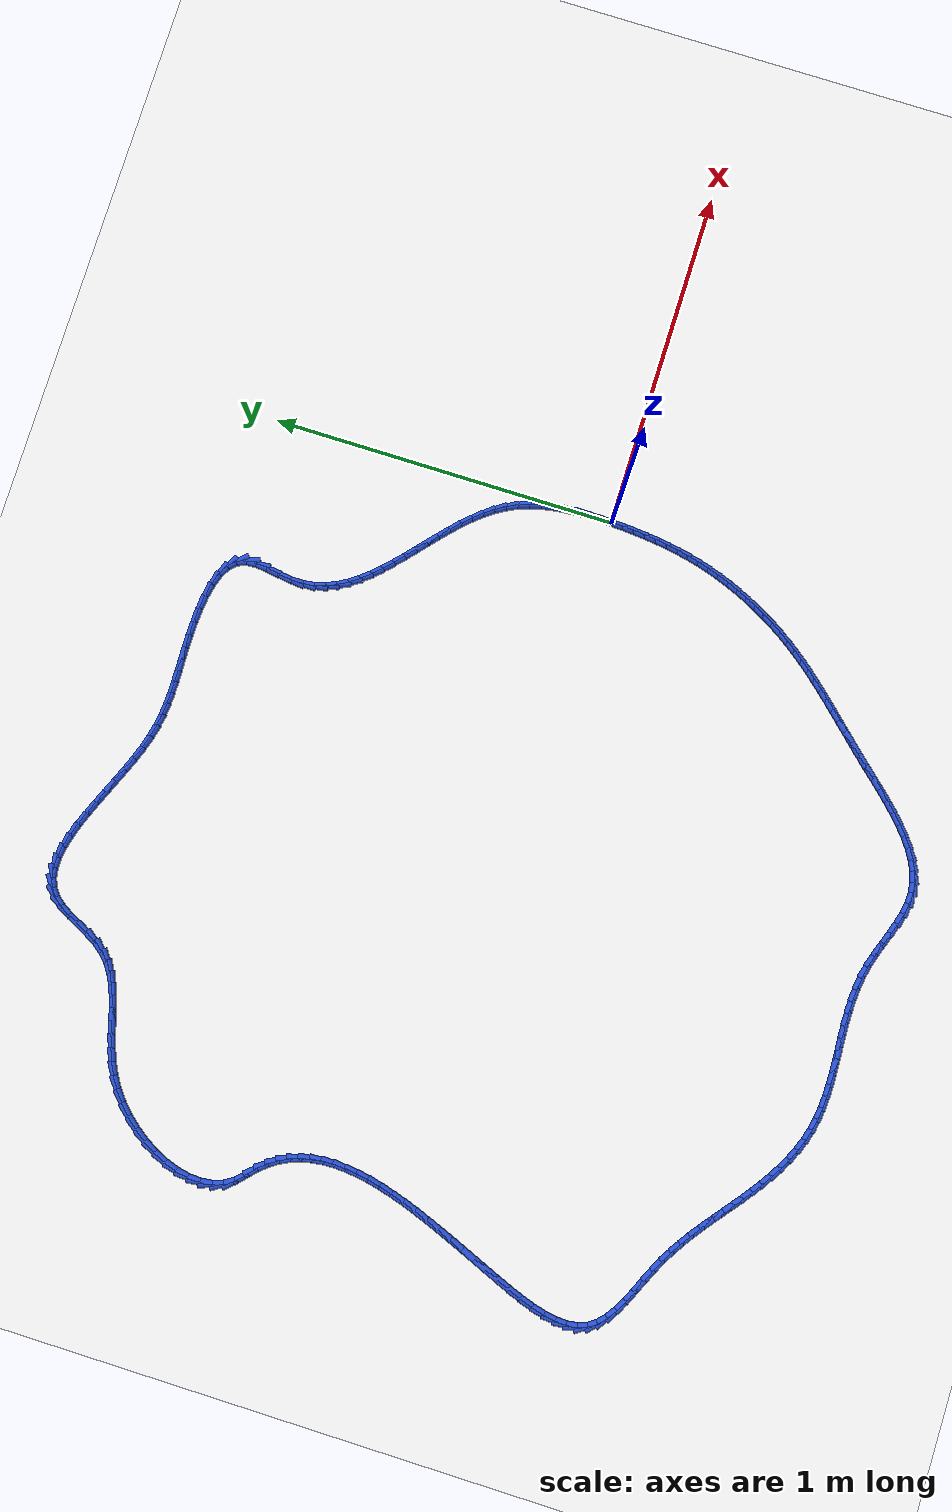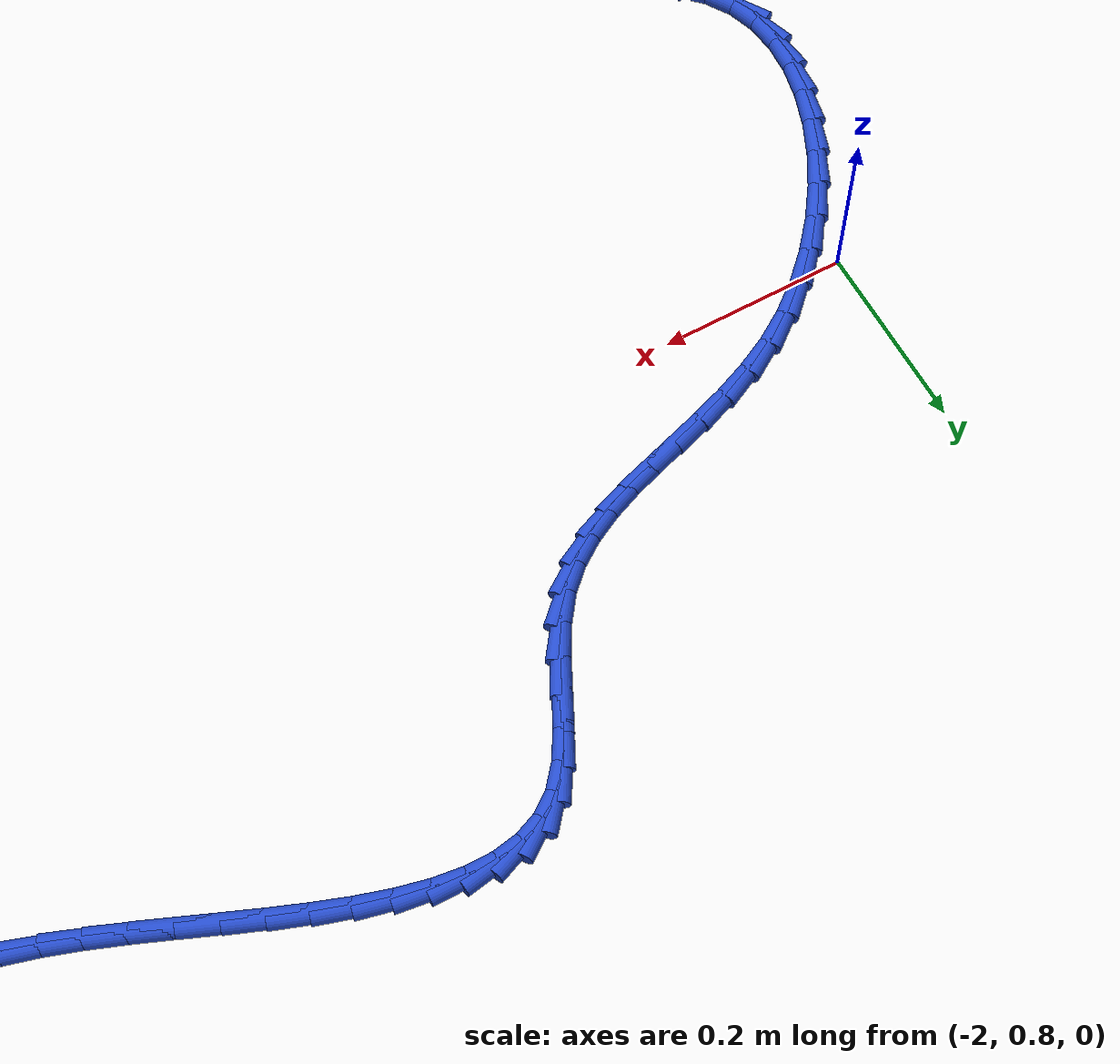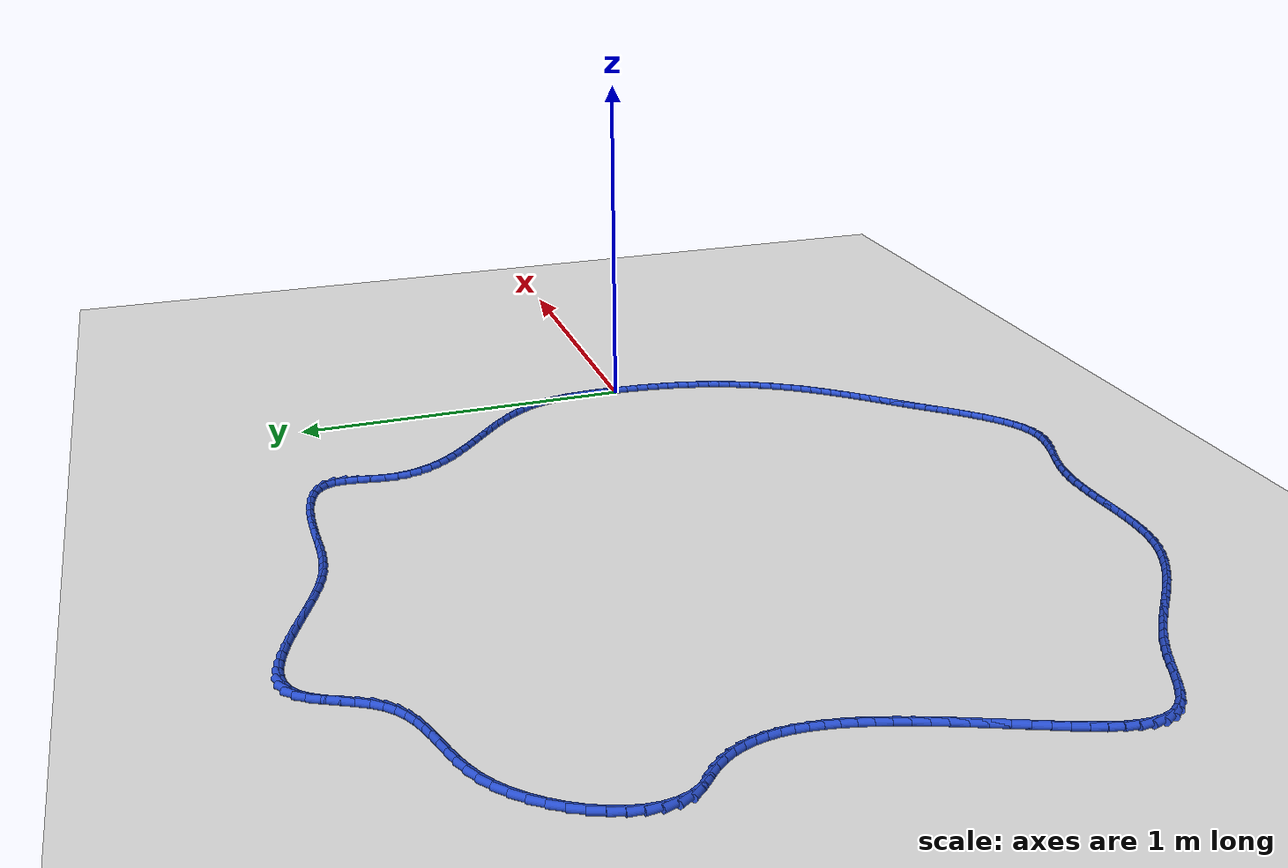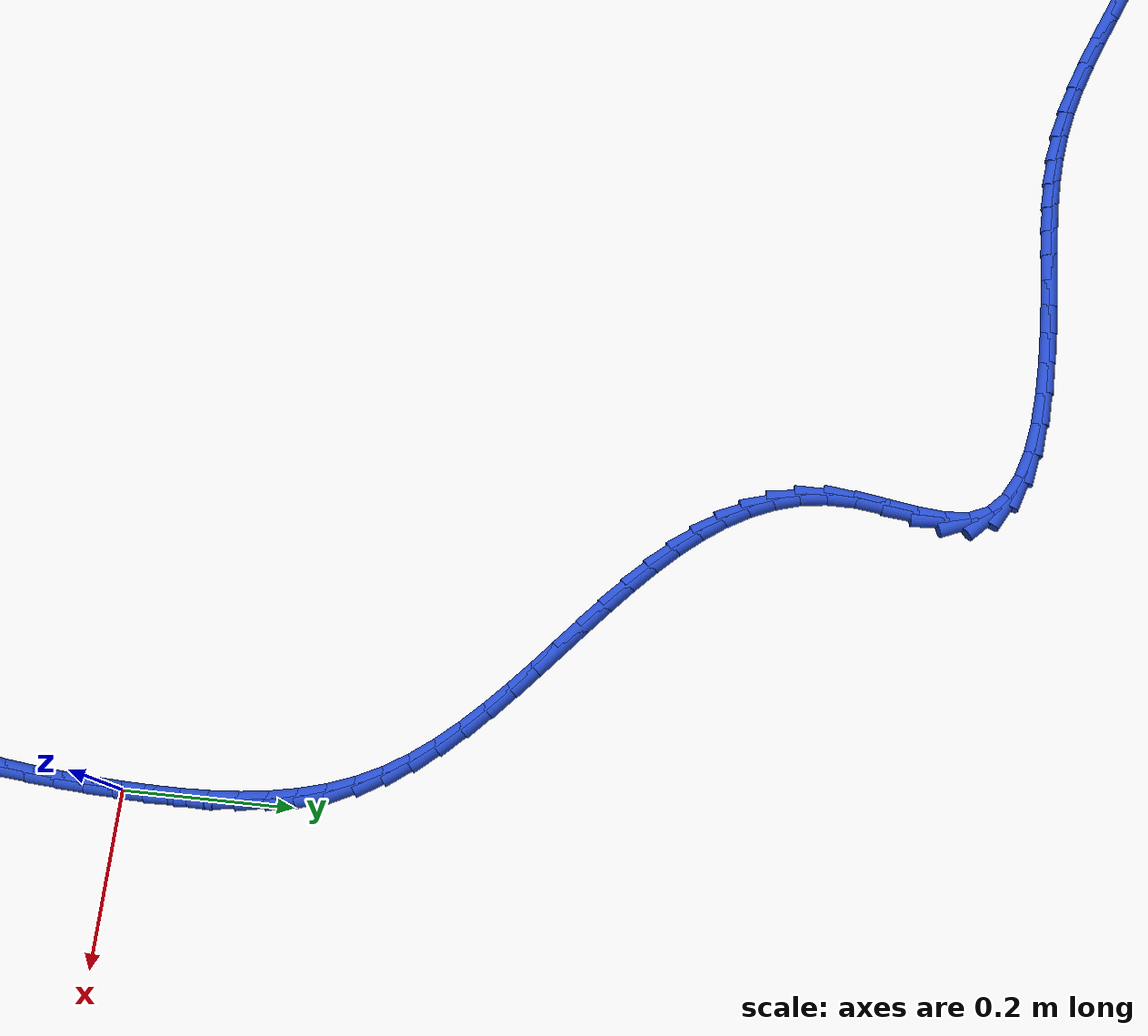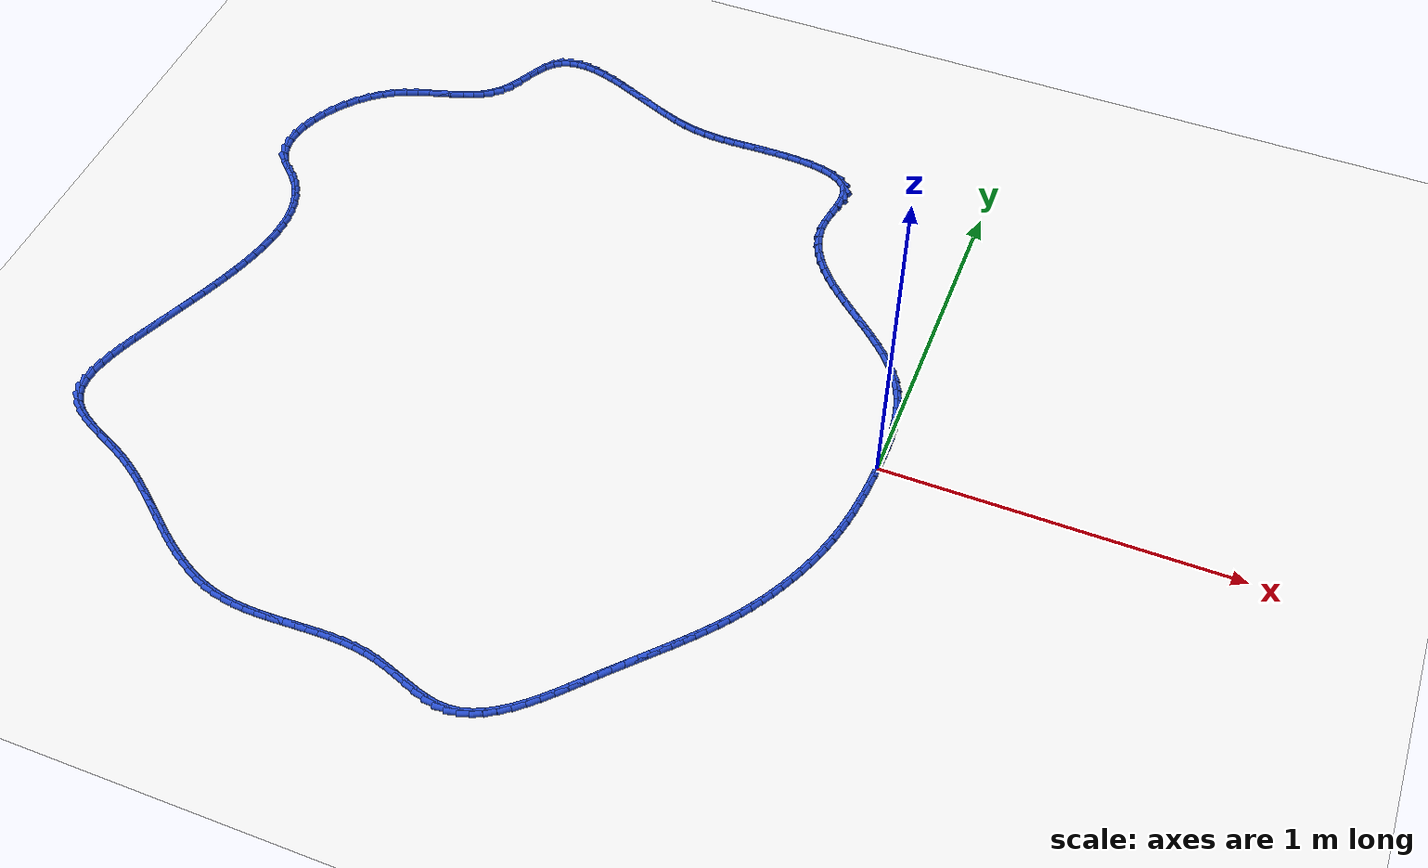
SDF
<sdf version="1.6">
 <world name="default">
  <light name="sun" type="directional">
   <pose>0 0 10 0 -0 0</pose>
   <diffuse>0.8 0.8 0.8 1</diffuse>
   <specular>0.2 0.2 0.2 1</specular>
   <attenuation>
    <range>1000</range>
    <constant>0.9</constant>
    <linear>0.01</linear>
    <quadratic>0.001</quadratic>
   </attenuation>
   <direction>-0.5 0.1 -0.9</direction>
  </light>
  <model name="ground_plane">
   <static>1</static>
   <link name="link">
    <collision name="collision">
     <geometry><plane><normal>0 0 1</normal><size>100 100</size></plane></geometry>
     <surface><friction><ode><mu>100</mu><mu2>50</mu2></ode></friction></surface>
    </collision>
    <visual name="visual">
     <cast_shadows>0</cast_shadows>
     <geometry><plane><normal>0 0 1</normal><size>100 100</size></plane></geometry>
     <material>
      <script><uri>file://media/materials/scripts/gazebo.material</uri><name>Gazebo/WhiteGlow</name></script>
     </material>
    </visual>
   </link>
  </model>
  <gravity>0 0 -9.8</gravity>
  <magnetic_field>6e-06 2.3e-05 -4.2e-05</magnetic_field>
  <atmosphere type="adiabatic"/>
  <physics name="default_physics" default="0" type="ode">
   <max_step_size>0.001</max_step_size>
   <real_time_factor>1</real_time_factor>
   <real_time_update_rate>1000</real_time_update_rate>
  </physics>
  <scene><ambient>0.4 0.4 0.4 1</ambient><background>0.7 0.7 0.7 1</background><shadows>1</shadows></scene>
  <spherical_coordinates>
   <surface_model>EARTH_WGS84</surface_model>
   <latitude_deg>0</latitude_deg>
   <longitude_deg>0</longitude_deg>
   <elevation>0</elevation>
   <heading_deg>0</heading_deg>
  </spherical_coordinates>
  <model name="line">
   <link name="link_0">
    <pose>-1.3660947373317356e-17 -4.163336342344337e-17 0.01 0 1.57 1.5384901847299584</pose>
    <collision name="collision">
     <geometry><cylinder><radius>0.01</radius><length>0.08</length></cylinder></geometry>
    </collision>
    <visual name="visual">
     <material>
      <script><name>Gazebo/Blue</name><uri>file://media/materials/scripts/gazebo.material</uri></script>
     </material>
     <geometry><cylinder><radius>0.01</radius><length>0.08</length></cylinder></geometry>
    </visual>
   </link>
   <link name="link_1">
    <pose>0.0011236001775610416 0.0347676690252532 0.01 0 1.57 1.5636642967160483</pose>
    <collision name="collision">
     <geometry><cylinder><radius>0.01</radius><length>0.08</length></cylinder></geometry>
    </collision>
    <visual name="visual">
     <material>
      <script><name>Gazebo/Blue</name><uri>file://media/materials/scripts/gazebo.material</uri></script>
     </material>
     <geometry><cylinder><radius>0.01</radius><length>0.08</length></cylinder></geometry>
    </visual>
   </link>
   <link name="link_2">
    <pose>0.0013723359309956262 0.06964294763246584 0.01 0 1.57 -1.5438584381845137</pose>
    <collision name="collision">
     <geometry><cylinder><radius>0.01</radius><length>0.08</length></cylinder></geometry>
    </collision>
    <visual name="visual">
     <material>
      <script><name>Gazebo/Blue</name><uri>file://media/materials/scripts/gazebo.material</uri></script>
     </material>
     <geometry><cylinder><radius>0.01</radius><length>0.08</length></cylinder></geometry>
    </visual>
   </link>
   <link name="link_3">
    <pose>0.0004349520113933465 0.10443250314252683 0.01 0 1.57 -1.5003617857551466</pose>
    <collision name="collision">
     <geometry><cylinder><radius>0.01</radius><length>0.08</length></cylinder></geometry>
    </collision>
    <visual name="visual">
     <material>
      <script><name>Gazebo/Blue</name><uri>file://media/materials/scripts/gazebo.material</uri></script>
     </material>
     <geometry><cylinder><radius>0.01</radius><length>0.08</length></cylinder></geometry>
    </visual>
   </link>
   <link name="link_4">
    <pose>-0.001999806830156192 0.13894300287632502 0.01 0 1.57 -1.4467703857361287</pose>
    <collision name="collision">
     <geometry><cylinder><radius>0.01</radius><length>0.08</length></cylinder></geometry>
    </collision>
    <visual name="visual">
     <material>
      <script><name>Gazebo/Blue</name><uri>file://media/materials/scripts/gazebo.material</uri></script>
     </material>
     <geometry><cylinder><radius>0.01</radius><length>0.08</length></cylinder></geometry>
    </visual>
   </link>
   <link name="link_5">
    <pose>-0.006243195842563384 0.1729811141547494 0.01 0 1.57 -1.382383154661688</pose>
    <collision name="collision">
     <geometry><cylinder><radius>0.01</radius><length>0.08</length></cylinder></geometry>
    </collision>
    <visual name="visual">
     <material>
      <script><name>Gazebo/Blue</name><uri>file://media/materials/scripts/gazebo.material</uri></script>
     </material>
     <geometry><cylinder><radius>0.01</radius><length>0.08</length></cylinder></geometry>
    </visual>
   </link>
   <link name="link_6">
    <pose>-0.01260647027473862 0.20635350429868887 0.01 0 1.57 -1.306631202709869</pose>
    <collision name="collision">
     <geometry><cylinder><radius>0.01</radius><length>0.08</length></cylinder></geometry>
    </collision>
    <visual name="visual">
     <material>
      <script><name>Gazebo/Blue</name><uri>file://media/materials/scripts/gazebo.material</uri></script>
     </material>
     <geometry><cylinder><radius>0.01</radius><length>0.08</length></cylinder></geometry>
    </visual>
   </link>
   <link name="link_7">
    <pose>-0.021400885375592312 0.2388668406290323 0.01 0 1.57 -1.2193198887436778</pose>
    <collision name="collision">
     <geometry><cylinder><radius>0.01</radius><length>0.08</length></cylinder></geometry>
    </collision>
    <visual name="visual">
     <material>
      <script><name>Gazebo/Blue</name><uri>file://media/materials/scripts/gazebo.material</uri></script>
     </material>
     <geometry><cylinder><radius>0.01</radius><length>0.08</length></cylinder></geometry>
    </visual>
   </link>
   <link name="link_8">
    <pose>-0.03293769639403482 0.27032779046666855 0.01 0 1.57 -1.120965788050166</pose>
    <collision name="collision">
     <geometry><cylinder><radius>0.01</radius><length>0.08</length></cylinder></geometry>
    </collision>
    <visual name="visual">
     <material>
      <script><name>Gazebo/Blue</name><uri>file://media/materials/scripts/gazebo.material</uri></script>
     </material>
     <geometry><cylinder><radius>0.01</radius><length>0.08</length></cylinder></geometry>
    </visual>
   </link>
   <link name="link_9">
    <pose>-0.04752722354716291 0.3005434798705982 0.01 0 1.57 -1.0199367805898423</pose>
    <collision name="collision">
     <geometry><cylinder><radius>0.01</radius><length>0.08</length></cylinder></geometry>
    </collision>
    <visual name="visual">
     <material>
      <script><name>Gazebo/Blue</name><uri>file://media/materials/scripts/gazebo.material</uri></script>
     </material>
     <geometry><cylinder><radius>0.01</radius><length>0.08</length></cylinder></geometry>
    </visual>
   </link>
   <link name="link_10">
    <pose>-0.06526859327880014 0.32942464916334213 0.01 0 1.57 -0.9331966750000591</pose>
    <collision name="collision">
     <geometry><cylinder><radius>0.01</radius><length>0.08</length></cylinder></geometry>
    </collision>
    <visual name="visual">
     <material>
      <script><name>Gazebo/Blue</name><uri>file://media/materials/scripts/gazebo.material</uri></script>
     </material>
     <geometry><cylinder><radius>0.01</radius><length>0.08</length></cylinder></geometry>
    </visual>
   </link>
   <link name="link_11">
    <pose>-0.08578319782332511 0.3571164209482183 0.01 0 1.57 -0.8627052753541691</pose>
    <collision name="collision">
     <geometry><cylinder><radius>0.01</radius><length>0.08</length></cylinder></geometry>
    </collision>
    <visual name="visual">
     <material>
      <script><name>Gazebo/Blue</name><uri>file://media/materials/scripts/gazebo.material</uri></script>
     </material>
     <geometry><cylinder><radius>0.01</radius><length>0.08</length></cylinder></geometry>
    </visual>
   </link>
   <link name="link_12">
    <pose>-0.1086267640760308 0.38379613405179236 0.01 0 1.57 -0.8074761785815207</pose>
    <collision name="collision">
     <geometry><cylinder><radius>0.01</radius><length>0.08</length></cylinder></geometry>
    </collision>
    <visual name="visual">
     <material>
      <script><name>Gazebo/Blue</name><uri>file://media/materials/scripts/gazebo.material</uri></script>
     </material>
     <geometry><cylinder><radius>0.01</radius><length>0.08</length></cylinder></geometry>
    </visual>
   </link>
   <link name="link_13">
    <pose>-0.13335501893221036 0.4096411273006293 0.01 0 1.57 -0.7662975047435123</pose>
    <collision name="collision">
     <geometry><cylinder><radius>0.01</radius><length>0.08</length></cylinder></geometry>
    </collision>
    <visual name="visual">
     <material>
      <script><name>Gazebo/Blue</name><uri>file://media/materials/scripts/gazebo.material</uri></script>
     </material>
     <geometry><cylinder><radius>0.01</radius><length>0.08</length></cylinder></geometry>
    </visual>
   </link>
   <link name="link_14">
    <pose>-0.15952368928715696 0.43482873952129464 0.01 0 1.57 -0.7380626247459453</pose>
    <collision name="collision">
     <geometry><cylinder><radius>0.01</radius><length>0.08</length></cylinder></geometry>
    </collision>
    <visual name="visual">
     <material>
      <script><name>Gazebo/Blue</name><uri>file://media/materials/scripts/gazebo.material</uri></script>
     </material>
     <geometry><cylinder><radius>0.01</radius><length>0.08</length></cylinder></geometry>
    </visual>
   </link>
   <link name="link_15">
    <pose>-0.18668850203616344 0.4595363095403535 0.01 0 1.57 -0.7219432345789546</pose>
    <collision name="collision">
     <geometry><cylinder><radius>0.01</radius><length>0.08</length></cylinder></geometry>
    </collision>
    <visual name="visual">
     <material>
      <script><name>Gazebo/Blue</name><uri>file://media/materials/scripts/gazebo.material</uri></script>
     </material>
     <geometry><cylinder><radius>0.01</radius><length>0.08</length></cylinder></geometry>
    </visual>
   </link>
   <link name="link_16">
    <pose>-0.214405184074523 0.48394117618437127 0.01 0 1.57 -0.7174698430547922</pose>
    <collision name="collision">
     <geometry><cylinder><radius>0.01</radius><length>0.08</length></cylinder></geometry>
    </collision>
    <visual name="visual">
     <material>
      <script><name>Gazebo/Blue</name><uri>file://media/materials/scripts/gazebo.material</uri></script>
     </material>
     <geometry><cylinder><radius>0.01</radius><length>0.08</length></cylinder></geometry>
    </visual>
   </link>
   <link name="link_17">
    <pose>-0.24222946229752865 0.5082206782799132 0.01 0 1.57 -0.7245666885214453</pose>
    <collision name="collision">
     <geometry><cylinder><radius>0.01</radius><length>0.08</length></cylinder></geometry>
    </collision>
    <visual name="visual">
     <material>
      <script><name>Gazebo/Blue</name><uri>file://media/materials/scripts/gazebo.material</uri></script>
     </material>
     <geometry><cylinder><radius>0.01</radius><length>0.08</length></cylinder></geometry>
    </visual>
   </link>
   <link name="link_18">
    <pose>-0.26971706360047354 0.5325521546535448 0.01 0 1.57 -0.7435663508352207</pose>
    <collision name="collision">
     <geometry><cylinder><radius>0.01</radius><length>0.08</length></cylinder></geometry>
    </collision>
    <visual name="visual">
     <material>
      <script><name>Gazebo/Blue</name><uri>file://media/materials/scripts/gazebo.material</uri></script>
     </material>
     <geometry><cylinder><radius>0.01</radius><length>0.08</length></cylinder></geometry>
    </visual>
   </link>
   <link name="link_19">
    <pose>-0.29642371487865077 0.5571129441318312 0.01 0 1.57 -0.7752102451999536</pose>
    <collision name="collision">
     <geometry><cylinder><radius>0.01</radius><length>0.08</length></cylinder></geometry>
    </collision>
    <visual name="visual">
     <material>
      <script><name>Gazebo/Blue</name><uri>file://media/materials/scripts/gazebo.material</uri></script>
     </material>
     <geometry><cylinder><radius>0.01</radius><length>0.08</length></cylinder></geometry>
    </visual>
   </link>
   <link name="link_20">
    <pose>-0.3219051430273532 0.5820803855413376 0.01 0 1.57 -0.820622277558166</pose>
    <collision name="collision">
     <geometry><cylinder><radius>0.01</radius><length>0.08</length></cylinder></geometry>
    </collision>
    <visual name="visual">
     <material>
      <script><name>Gazebo/Blue</name><uri>file://media/materials/scripts/gazebo.material</uri></script>
     </material>
     <geometry><cylinder><radius>0.01</radius><length>0.08</length></cylinder></geometry>
    </visual>
   </link>
   <link name="link_21">
    <pose>-0.34571707494187415 0.6076318177086295 0.01 0 1.57 -0.8812194223791564</pose>
    <collision name="collision">
     <geometry><cylinder><radius>0.01</radius><length>0.08</length></cylinder></geometry>
    </collision>
    <visual name="visual">
     <material>
      <script><name>Gazebo/Blue</name><uri>file://media/materials/scripts/gazebo.material</uri></script>
     </material>
     <geometry><cylinder><radius>0.01</radius><length>0.08</length></cylinder></geometry>
    </visual>
   </link>
   <link name="link_22">
    <pose>-0.3674152375175065 0.633944579460272 0.01 0 1.57 -0.9584930012429872</pose>
    <collision name="collision">
     <geometry><cylinder><radius>0.01</radius><length>0.08</length></cylinder></geometry>
    </collision>
    <visual name="visual">
     <material>
      <script><name>Gazebo/Blue</name><uri>file://media/materials/scripts/gazebo.material</uri></script>
     </material>
     <geometry><cylinder><radius>0.01</radius><length>0.08</length></cylinder></geometry>
    </visual>
   </link>
   <link name="link_23">
    <pose>-0.38655535764954324 0.6611960096228303 0.01 0 1.57 -1.053569909252011</pose>
    <collision name="collision">
     <geometry><cylinder><radius>0.01</radius><length>0.08</length></cylinder></geometry>
    </collision>
    <visual name="visual">
     <material>
      <script><name>Gazebo/Blue</name><uri>file://media/materials/scripts/gazebo.material</uri></script>
     </material>
     <geometry><cylinder><radius>0.01</radius><length>0.08</length></cylinder></geometry>
    </visual>
   </link>
   <link name="link_24">
    <pose>-0.40269316223327783 0.6895634470228704 0.01 0 1.57 -1.1664899673265698</pose>
    <collision name="collision">
     <geometry><cylinder><radius>0.01</radius><length>0.08</length></cylinder></geometry>
    </collision>
    <visual name="visual">
     <material>
      <script><name>Gazebo/Blue</name><uri>file://media/materials/scripts/gazebo.material</uri></script>
     </material>
     <geometry><cylinder><radius>0.01</radius><length>0.08</length></cylinder></geometry>
    </visual>
   </link>
   <link name="link_25">
    <pose>-0.415384378164003 0.7192242304869567 0.01 0 1.57 -1.2953009009751486</pose>
    <collision name="collision">
     <geometry><cylinder><radius>0.01</radius><length>0.08</length></cylinder></geometry>
    </collision>
    <visual name="visual">
     <material>
      <script><name>Gazebo/Blue</name><uri>file://media/materials/scripts/gazebo.material</uri></script>
     </material>
     <geometry><cylinder><radius>0.01</radius><length>0.08</length></cylinder></geometry>
    </visual>
   </link>
   <link name="link_26">
    <pose>-0.42418473233701187 0.7503556988416551 0.01 0 1.57 -1.4354097225507094</pose>
    <collision name="collision">
     <geometry><cylinder><radius>0.01</radius><length>0.08</length></cylinder></geometry>
    </collision>
    <visual name="visual">
     <material>
      <script><name>Gazebo/Blue</name><uri>file://media/materials/scripts/gazebo.material</uri></script>
     </material>
     <geometry><cylinder><radius>0.01</radius><length>0.08</length></cylinder></geometry>
    </visual>
   </link>
   <link name="link_27">
    <pose>-0.42864995164759767 0.7831351909135309 0.01 0 1.57 1.5617885875148487</pose>
    <collision name="collision">
     <geometry><cylinder><radius>0.01</radius><length>0.08</length></cylinder></geometry>
    </collision>
    <visual name="visual">
     <material>
      <script><name>Gazebo/Blue</name><uri>file://media/materials/scripts/gazebo.material</uri></script>
     </material>
     <geometry><cylinder><radius>0.01</radius><length>0.08</length></cylinder></geometry>
    </visual>
   </link>
   <link name="link_28">
    <pose>-0.4283382429153973 0.8177388014142021 0.01 0 1.57 1.4454517126386108</pose>
    <collision name="collision">
     <geometry><cylinder><radius>0.01</radius><length>0.08</length></cylinder></geometry>
    </collision>
    <visual name="visual">
     <material>
      <script><name>Gazebo/Blue</name><uri>file://media/materials/scripts/gazebo.material</uri></script>
     </material>
     <geometry><cylinder><radius>0.01</radius><length>0.08</length></cylinder></geometry>
    </visual>
   </link>
   <link name="link_29">
    <pose>-0.4237879270858374 0.8538509267352312 0.01 0 1.57 1.4118350441793106</pose>
    <collision name="collision">
     <geometry><cylinder><radius>0.01</radius><length>0.08</length></cylinder></geometry>
    </collision>
    <visual name="visual">
     <material>
      <script><name>Gazebo/Blue</name><uri>file://media/materials/scripts/gazebo.material</uri></script>
     </material>
     <geometry><cylinder><radius>0.01</radius><length>0.08</length></cylinder></geometry>
    </visual>
   </link>
   <link name="link_30">
    <pose>-0.4180059526432179 0.8899175156407436 0.01 0 1.57 1.4654519796701009</pose>
    <collision name="collision">
     <geometry><cylinder><radius>0.01</radius><length>0.08</length></cylinder></geometry>
    </collision>
    <visual name="visual">
     <material>
      <script><name>Gazebo/Blue</name><uri>file://media/materials/scripts/gazebo.material</uri></script>
     </material>
     <geometry><cylinder><radius>0.01</radius><length>0.08</length></cylinder></geometry>
    </visual>
   </link>
   <link name="link_31">
    <pose>-0.4143818519124362 0.9241925843160399 0.01 0 1.57 -1.508305978367452</pose>
    <collision name="collision">
     <geometry><cylinder><radius>0.01</radius><length>0.08</length></cylinder></geometry>
    </collision>
    <visual name="visual">
     <material>
      <script><name>Gazebo/Blue</name><uri>file://media/materials/scripts/gazebo.material</uri></script>
     </material>
     <geometry><cylinder><radius>0.01</radius><length>0.08</length></cylinder></geometry>
    </visual>
   </link>
   <link name="link_32">
    <pose>-0.4163051572183906 0.954930148946423 0.01 0 1.57 -1.176267296860016</pose>
    <collision name="collision">
     <geometry><cylinder><radius>0.01</radius><length>0.08</length></cylinder></geometry>
    </collision>
    <visual name="visual">
     <material>
      <script><name>Gazebo/Blue</name><uri>file://media/materials/scripts/gazebo.material</uri></script>
     </material>
     <geometry><cylinder><radius>0.01</radius><length>0.08</length></cylinder></geometry>
    </visual>
   </link>
   <link name="link_33">
    <pose>-0.4269466669309595 0.9804886379719094 0.01 0 1.57 -0.7943941027103802</pose>
    <collision name="collision">
     <geometry><cylinder><radius>0.01</radius><length>0.08</length></cylinder></geometry>
    </collision>
    <visual name="visual">
     <material>
      <script><name>Gazebo/Blue</name><uri>file://media/materials/scripts/gazebo.material</uri></script>
     </material>
     <geometry><cylinder><radius>0.01</radius><length>0.08</length></cylinder></geometry>
    </visual>
   </link>
   <link name="link_34">
    <pose>-0.44666760611306816 1.000567624529239 0.01 0 1.57 -0.5101871442627651</pose>
    <collision name="collision">
     <geometry><cylinder><radius>0.01</radius><length>0.08</length></cylinder></geometry>
    </collision>
    <visual name="visual">
     <material>
      <script><name>Gazebo/Blue</name><uri>file://media/materials/scripts/gazebo.material</uri></script>
     </material>
     <geometry><cylinder><radius>0.01</radius><length>0.08</length></cylinder></geometry>
    </visual>
   </link>
   <link name="link_35">
    <pose>-0.4738812804592791 1.015796517514928 0.01 0 1.57 -0.32175108508715977</pose>
    <collision name="collision">
     <geometry><cylinder><radius>0.01</radius><length>0.08</length></cylinder></geometry>
    </collision>
    <visual name="visual">
     <material>
      <script><name>Gazebo/Blue</name><uri>file://media/materials/scripts/gazebo.material</uri></script>
     </material>
     <geometry><cylinder><radius>0.01</radius><length>0.08</length></cylinder></geometry>
    </visual>
   </link>
   <link name="link_36">
    <pose>-0.5069618726997189 1.026823401101252 0.01 0 1.57 -0.1976176260841162</pose>
    <collision name="collision">
     <geometry><cylinder><radius>0.01</radius><length>0.08</length></cylinder></geometry>
    </collision>
    <visual name="visual">
     <material>
      <script><name>Gazebo/Blue</name><uri>file://media/materials/scripts/gazebo.material</uri></script>
     </material>
     <geometry><cylinder><radius>0.01</radius><length>0.08</length></cylinder></geometry>
    </visual>
   </link>
   <link name="link_37">
    <pose>-0.5442835655645152 1.034296359460487 0.01 0 1.57 -0.11386347345799201</pose>
    <collision name="collision">
     <geometry><cylinder><radius>0.01</radius><length>0.08</length></cylinder></geometry>
    </collision>
    <visual name="visual">
     <material>
      <script><name>Gazebo/Blue</name><uri>file://media/materials/scripts/gazebo.material</uri></script>
     </material>
     <geometry><cylinder><radius>0.01</radius><length>0.08</length></cylinder></geometry>
    </visual>
   </link>
   <link name="link_38">
    <pose>-0.5842205417837948 1.0388634767649083 0.01 0 1.57 -0.05636732511187883</pose>
    <collision name="collision">
     <geometry><cylinder><radius>0.01</radius><length>0.08</length></cylinder></geometry>
    </collision>
    <visual name="visual">
     <material>
      <script><name>Gazebo/Blue</name><uri>file://media/materials/scripts/gazebo.material</uri></script>
     </material>
     <geometry><cylinder><radius>0.01</radius><length>0.08</length></cylinder></geometry>
    </visual>
   </link>
   <link name="link_39">
    <pose>-0.6251469840876843 1.0411728371867917 0.01 0 1.57 -0.017364502440103024</pose>
    <collision name="collision">
     <geometry><cylinder><radius>0.01</radius><length>0.08</length></cylinder></geometry>
    </collision>
    <visual name="visual">
     <material>
      <script><name>Gazebo/Blue</name><uri>file://media/materials/scripts/gazebo.material</uri></script>
     </material>
     <geometry><cylinder><radius>0.01</radius><length>0.08</length></cylinder></geometry>
    </visual>
   </link>
   <link name="link_40">
    <pose>-0.6654370752063115 1.0418725248984129 0.01 0 1.57 0.007525057697815429</pose>
    <collision name="collision">
     <geometry><cylinder><radius>0.01</radius><length>0.08</length></cylinder></geometry>
    </collision>
    <visual name="visual">
     <material>
      <script><name>Gazebo/Blue</name><uri>file://media/materials/scripts/gazebo.material</uri></script>
     </material>
     <geometry><cylinder><radius>0.01</radius><length>0.08</length></cylinder></geometry>
    </visual>
   </link>
   <link name="link_41">
    <pose>-0.7036985361444995 1.0415845997624995 0.01 0 1.57 0.022180041345182352</pose>
    <collision name="collision">
     <geometry><cylinder><radius>0.01</radius><length>0.08</length></cylinder></geometry>
    </collision>
    <visual name="visual">
     <material>
      <script><name>Gazebo/Blue</name><uri>file://media/materials/scripts/gazebo.material</uri></script>
     </material>
     <geometry><cylinder><radius>0.01</radius><length>0.08</length></cylinder></geometry>
    </visual>
   </link>
   <link name="link_42">
    <pose>-0.7398770363474706 1.0407820275182698 0.01 0 1.57 0.025988859347803008</pose>
    <collision name="collision">
     <geometry><cylinder><radius>0.01</radius><length>0.08</length></cylinder></geometry>
    </collision>
    <visual name="visual">
     <material>
      <script><name>Gazebo/Blue</name><uri>file://media/materials/scripts/gazebo.material</uri></script>
     </material>
     <geometry><cylinder><radius>0.01</radius><length>0.08</length></cylinder></geometry>
    </visual>
   </link>
   <link name="link_43">
    <pose>-0.7743938741353531 1.0398847722584814 0.01 0 1.57 0.0171884725797061</pose>
    <collision name="collision">
     <geometry><cylinder><radius>0.01</radius><length>0.08</length></cylinder></geometry>
    </collision>
    <visual name="visual">
     <material>
      <script><name>Gazebo/Blue</name><uri>file://media/materials/scripts/gazebo.material</uri></script>
     </material>
     <geometry><cylinder><radius>0.01</radius><length>0.08</length></cylinder></geometry>
    </visual>
   </link>
   <link name="link_44">
    <pose>-0.8076709198301236 1.0393127343349344 0.01 0 1.57 -0.005332187170313639</pose>
    <collision name="collision">
     <geometry><cylinder><radius>0.01</radius><length>0.08</length></cylinder></geometry>
    </collision>
    <visual name="visual">
     <material>
      <script><name>Gazebo/Blue</name><uri>file://media/materials/scripts/gazebo.material</uri></script>
     </material>
     <geometry><cylinder><radius>0.01</radius><length>0.08</length></cylinder></geometry>
    </visual>
   </link>
   <link name="link_45">
    <pose>-0.8401300437537591 1.03948581409943 0.01 0 1.57 -0.04170909619967235</pose>
    <collision name="collision">
     <geometry><cylinder><radius>0.01</radius><length>0.08</length></cylinder></geometry>
    </collision>
    <visual name="visual">
     <material>
      <script><name>Gazebo/Blue</name><uri>file://media/materials/scripts/gazebo.material</uri></script>
     </material>
     <geometry><cylinder><radius>0.01</radius><length>0.08</length></cylinder></geometry>
    </visual>
   </link>
   <link name="link_46">
    <pose>-0.8721931162282368 1.0408239119037688 0.01 0 1.57 -0.09084051844408403</pose>
    <collision name="collision">
     <geometry><cylinder><radius>0.01</radius><length>0.08</length></cylinder></geometry>
    </collision>
    <visual name="visual">
     <material>
      <script><name>Gazebo/Blue</name><uri>file://media/materials/scripts/gazebo.material</uri></script>
     </material>
     <geometry><cylinder><radius>0.01</radius><length>0.08</length></cylinder></geometry>
    </visual>
   </link>
   <link name="link_47">
    <pose>-0.904282007575533 1.0437469280997507 0.01 0 1.57 -0.15031284019430727</pose>
    <collision name="collision">
     <geometry><cylinder><radius>0.01</radius><length>0.08</length></cylinder></geometry>
    </collision>
    <visual name="visual">
     <material>
      <script><name>Gazebo/Blue</name><uri>file://media/materials/scripts/gazebo.material</uri></script>
     </material>
     <geometry><cylinder><radius>0.01</radius><length>0.08</length></cylinder></geometry>
    </visual>
   </link>
   <link name="link_48">
    <pose>-0.9368185881176252 1.048674763039176 0.01 0 1.57 -0.21664176366071328</pose>
    <collision name="collision">
     <geometry><cylinder><radius>0.01</radius><length>0.08</length></cylinder></geometry>
    </collision>
    <visual name="visual">
     <material>
      <script><name>Gazebo/Blue</name><uri>file://media/materials/scripts/gazebo.material</uri></script>
     </material>
     <geometry><cylinder><radius>0.01</radius><length>0.08</length></cylinder></geometry>
    </visual>
   </link>
   <link name="link_49">
    <pose>-0.9702247281764903 1.056027317073846 0.01 0 1.57 -0.28445234879375075</pose>
    <collision name="collision">
     <geometry><cylinder><radius>0.01</radius><length>0.08</length></cylinder></geometry>
    </collision>
    <visual name="visual">
     <material>
      <script><name>Gazebo/Blue</name><uri>file://media/materials/scripts/gazebo.material</uri></script>
     </material>
     <geometry><cylinder><radius>0.01</radius><length>0.08</length></cylinder></geometry>
    </visual>
   </link>
   <link name="link_50">
    <pose>-1.0048782815031003 1.066159359020659 0.01 0 1.57 -0.3384817668990038</pose>
    <collision name="collision">
     <geometry><cylinder><radius>0.01</radius><length>0.08</length></cylinder></geometry>
    </collision>
    <visual name="visual">
     <material>
      <script><name>Gazebo/Blue</name><uri>file://media/materials/scripts/gazebo.material</uri></script>
     </material>
     <geometry><cylinder><radius>0.01</radius><length>0.08</length></cylinder></geometry>
    </visual>
   </link>
   <link name="link_51">
    <pose>-1.0407180742041144 1.078776026348917 0.01 0 1.57 -0.37458024553834374</pose>
    <collision name="collision">
     <geometry><cylinder><radius>0.01</radius><length>0.08</length></cylinder></geometry>
    </collision>
    <visual name="visual">
     <material>
      <script><name>Gazebo/Blue</name><uri>file://media/materials/scripts/gazebo.material</uri></script>
     </material>
     <geometry><cylinder><radius>0.01</radius><length>0.08</length></cylinder></geometry>
    </visual>
   </link>
   <link name="link_52">
    <pose>-1.0774307639176275 1.0932093216144898 0.01 0 1.57 -0.3959024256272547</pose>
    <collision name="collision">
     <geometry><cylinder><radius>0.01</radius><length>0.08</length></cylinder></geometry>
    </collision>
    <visual name="visual">
     <material>
      <script><name>Gazebo/Blue</name><uri>file://media/materials/scripts/gazebo.material</uri></script>
     </material>
     <geometry><cylinder><radius>0.01</radius><length>0.08</length></cylinder></geometry>
    </visual>
   </link>
   <link name="link_53">
    <pose>-1.1147000043149715 1.1087868023889695 0.01 0 1.57 -0.4043003505000687</pose>
    <collision name="collision">
     <geometry><cylinder><radius>0.01</radius><length>0.08</length></cylinder></geometry>
    </collision>
    <visual name="visual">
     <material>
      <script><name>Gazebo/Blue</name><uri>file://media/materials/scripts/gazebo.material</uri></script>
     </material>
     <geometry><cylinder><radius>0.01</radius><length>0.08</length></cylinder></geometry>
    </visual>
   </link>
   <link name="link_54">
    <pose>-1.152209449067476 1.1248360262439465 0.01 0 1.57 -0.40049798249615065</pose>
    <collision name="collision">
     <geometry><cylinder><radius>0.01</radius><length>0.08</length></cylinder></geometry>
    </collision>
    <visual name="visual">
     <material>
      <script><name>Gazebo/Blue</name><uri>file://media/materials/scripts/gazebo.material</uri></script>
     </material>
     <geometry><cylinder><radius>0.01</radius><length>0.08</length></cylinder></geometry>
    </visual>
   </link>
   <link name="link_55">
    <pose>-1.1896427518464734 1.1406845507510126 0.01 0 1.57 -0.3842026968703422</pose>
    <collision name="collision">
     <geometry><cylinder><radius>0.01</radius><length>0.08</length></cylinder></geometry>
    </collision>
    <visual name="visual">
     <material>
      <script><name>Gazebo/Blue</name><uri>file://media/materials/scripts/gazebo.material</uri></script>
     </material>
     <geometry><cylinder><radius>0.01</radius><length>0.08</length></cylinder></geometry>
    </visual>
   </link>
   <link name="link_56">
    <pose>-1.226683566323294 1.1556599334817588 0.01 0 1.57 -0.3540643331839261</pose>
    <collision name="collision">
     <geometry><cylinder><radius>0.01</radius><length>0.08</length></cylinder></geometry>
    </collision>
    <visual name="visual">
     <material>
      <script><name>Gazebo/Blue</name><uri>file://media/materials/scripts/gazebo.material</uri></script>
     </material>
     <geometry><cylinder><radius>0.01</radius><length>0.08</length></cylinder></geometry>
    </visual>
   </link>
   <link name="link_57">
    <pose>-1.263015546169269 1.1690897320077762 0.01 0 1.57 -0.30748146175503777</pose>
    <collision name="collision">
     <geometry><cylinder><radius>0.01</radius><length>0.08</length></cylinder></geometry>
    </collision>
    <visual name="visual">
     <material>
      <script><name>Gazebo/Blue</name><uri>file://media/materials/scripts/gazebo.material</uri></script>
     </material>
     <geometry><cylinder><radius>0.01</radius><length>0.08</length></cylinder></geometry>
    </visual>
   </link>
   <link name="link_58">
    <pose>-1.2983223450557293 1.1803015039006561 0.01 0 1.57 -0.24026203141074862</pose>
    <collision name="collision">
     <geometry><cylinder><radius>0.01</radius><length>0.08</length></cylinder></geometry>
    </collision>
    <visual name="visual">
     <material>
      <script><name>Gazebo/Blue</name><uri>file://media/materials/scripts/gazebo.material</uri></script>
     </material>
     <geometry><cylinder><radius>0.01</radius><length>0.08</length></cylinder></geometry>
    </visual>
   </link>
   <link name="link_59">
    <pose>-1.3322876166540063 1.18862280673199 0.01 0 1.57 -0.14623352493031438</pose>
    <collision name="collision">
     <geometry><cylinder><radius>0.01</radius><length>0.08</length></cylinder></geometry>
    </collision>
    <visual name="visual">
     <material>
      <script><name>Gazebo/Blue</name><uri>file://media/materials/scripts/gazebo.material</uri></script>
     </material>
     <geometry><cylinder><radius>0.01</radius><length>0.08</length></cylinder></geometry>
    </visual>
   </link>
   <link name="link_60">
    <pose>-1.364595014635431 1.1933811980733684 0.01 0 1.57 -0.017241371625488295</pose>
    <collision name="collision">
     <geometry><cylinder><radius>0.01</radius><length>0.08</length></cylinder></geometry>
    </collision>
    <visual name="visual">
     <material>
      <script><name>Gazebo/Blue</name><uri>file://media/materials/scripts/gazebo.material</uri></script>
     </material>
     <geometry><cylinder><radius>0.01</radius><length>0.08</length></cylinder></geometry>
    </visual>
   </link>
   <link name="link_61">
    <pose>-1.3949281926713337 1.193904235496383 0.01 0 1.57 0.15510468069740346</pose>
    <collision name="collision">
     <geometry><cylinder><radius>0.01</radius><length>0.08</length></cylinder></geometry>
    </collision>
    <visual name="visual">
     <material>
      <script><name>Gazebo/Blue</name><uri>file://media/materials/scripts/gazebo.material</uri></script>
     </material>
     <geometry><cylinder><radius>0.01</radius><length>0.08</length></cylinder></geometry>
    </visual>
   </link>
   <link name="link_62">
    <pose>-1.4229708044330467 1.1895194765726256 0.01 0 1.57 0.3733933126894242</pose>
    <collision name="collision">
     <geometry><cylinder><radius>0.01</radius><length>0.08</length></cylinder></geometry>
    </collision>
    <visual name="visual">
     <material>
      <script><name>Gazebo/Blue</name><uri>file://media/materials/scripts/gazebo.material</uri></script>
     </material>
     <geometry><cylinder><radius>0.01</radius><length>0.08</length></cylinder></geometry>
    </visual>
   </link>
   <link name="link_63">
    <pose>-1.4484065035919003 1.1795544788736865 0.01 0 1.57 0.6242781612145978</pose>
    <collision name="collision">
     <geometry><cylinder><radius>0.01</radius><length>0.08</length></cylinder></geometry>
    </collision>
    <visual name="visual">
     <material>
      <script><name>Gazebo/Blue</name><uri>file://media/materials/scripts/gazebo.material</uri></script>
     </material>
     <geometry><cylinder><radius>0.01</radius><length>0.08</length></cylinder></geometry>
    </visual>
   </link>
   <link name="link_64">
    <pose>-1.4709189438192252 1.163336799971157 0.01 0 1.57 0.8681256905886411</pose>
    <collision name="collision">
     <geometry><cylinder><radius>0.01</radius><length>0.08</length></cylinder></geometry>
    </collision>
    <visual name="visual">
     <material>
      <script><name>Gazebo/Blue</name><uri>file://media/materials/scripts/gazebo.material</uri></script>
     </material>
     <geometry><cylinder><radius>0.01</radius><length>0.08</length></cylinder></geometry>
    </visual>
   </link>
   <link name="link_65">
    <pose>-1.4903164485098914 1.1404316999327444 0.01 0 1.57 1.0266291930084523</pose>
    <collision name="collision">
     <geometry><cylinder><radius>0.01</radius><length>0.08</length></cylinder></geometry>
    </collision>
    <visual name="visual">
     <material>
      <script><name>Gazebo/Blue</name><uri>file://media/materials/scripts/gazebo.material</uri></script>
     </material>
     <geometry><cylinder><radius>0.01</radius><length>0.08</length></cylinder></geometry>
    </visual>
   </link>
   <link name="link_66">
    <pose>-1.5073725724766769 1.1122448048015792 0.01 0 1.57 1.0985582138030214</pose>
    <collision name="collision">
     <geometry><cylinder><radius>0.01</radius><length>0.08</length></cylinder></geometry>
    </collision>
    <visual name="visual">
     <material>
      <script><name>Gazebo/Blue</name><uri>file://media/materials/scripts/gazebo.material</uri></script>
     </material>
     <geometry><cylinder><radius>0.01</radius><length>0.08</length></cylinder></geometry>
    </visual>
   </link>
   <link name="link_67">
    <pose>-1.523311262605635 1.0810404841634105 0.01 0 1.57 1.1053610300656398</pose>
    <collision name="collision">
     <geometry><cylinder><radius>0.01</radius><length>0.08</length></cylinder></geometry>
    </collision>
    <visual name="visual">
     <material>
      <script><name>Gazebo/Blue</name><uri>file://media/materials/scripts/gazebo.material</uri></script>
     </material>
     <geometry><cylinder><radius>0.01</radius><length>0.08</length></cylinder></geometry>
    </visual>
   </link>
   <link name="link_68">
    <pose>-1.539359000185425 1.0490879398423834 0.01 0 1.57 1.0518038132027054</pose>
    <collision name="collision">
     <geometry><cylinder><radius>0.01</radius><length>0.08</length></cylinder></geometry>
    </collision>
    <visual name="visual">
     <material>
      <script><name>Gazebo/Blue</name><uri>file://media/materials/scripts/gazebo.material</uri></script>
     </material>
     <geometry><cylinder><radius>0.01</radius><length>0.08</length></cylinder></geometry>
    </visual>
   </link>
   <link name="link_69">
    <pose>-1.5567422665047042 1.0186563736626426 0.01 0 1.57 0.9287650312869475</pose>
    <collision name="collision">
     <geometry><cylinder><radius>0.01</radius><length>0.08</length></cylinder></geometry>
    </collision>
    <visual name="visual">
     <material>
      <script><name>Gazebo/Blue</name><uri>file://media/materials/scripts/gazebo.material</uri></script>
     </material>
     <geometry><cylinder><radius>0.01</radius><length>0.08</length></cylinder></geometry>
    </visual>
   </link>
   <link name="link_70">
    <pose>-1.5766771100107988 0.9919950321727288 0.01 0 1.57 0.7570099110917674</pose>
    <collision name="collision">
     <geometry><cylinder><radius>0.01</radius><length>0.08</length></cylinder></geometry>
    </collision>
    <visual name="visual">
     <material>
      <script><name>Gazebo/Blue</name><uri>file://media/materials/scripts/gazebo.material</uri></script>
     </material>
     <geometry><cylinder><radius>0.01</radius><length>0.08</length></cylinder></geometry>
    </visual>
   </link>
   <link name="link_71">
    <pose>-1.5997665767066234 0.9701806498187563 0.01 0 1.57 0.5992589299482725</pose>
    <collision name="collision">
     <geometry><cylinder><radius>0.01</radius><length>0.08</length></cylinder></geometry>
    </collision>
    <visual name="visual">
     <material>
      <script><name>Gazebo/Blue</name><uri>file://media/materials/scripts/gazebo.material</uri></script>
     </material>
     <geometry><cylinder><radius>0.01</radius><length>0.08</length></cylinder></geometry>
    </visual>
   </link>
   <link name="link_72">
    <pose>-1.6256709413481314 0.9524866881448151 0.01 0 1.57 0.4722020520295158</pose>
    <collision name="collision">
     <geometry><cylinder><radius>0.01</radius><length>0.08</length></cylinder></geometry>
    </collision>
    <visual name="visual">
     <material>
      <script><name>Gazebo/Blue</name><uri>file://media/materials/scripts/gazebo.material</uri></script>
     </material>
     <geometry><cylinder><radius>0.01</radius><length>0.08</length></cylinder></geometry>
    </visual>
   </link>
   <link name="link_73">
    <pose>-1.6539702368437892 0.9380331271907041 0.01 0 1.57 0.3800357765153801</pose>
    <collision name="collision">
     <geometry><cylinder><radius>0.01</radius><length>0.08</length></cylinder></geometry>
    </collision>
    <visual name="visual">
     <material>
      <script><name>Gazebo/Blue</name><uri>file://media/materials/scripts/gazebo.material</uri></script>
     </material>
     <geometry><cylinder><radius>0.01</radius><length>0.08</length></cylinder></geometry>
    </visual>
   </link>
   <link name="link_74">
    <pose>-1.6842444961020613 0.9259399469962228 0.01 0 1.57 0.32183728582792975</pose>
    <collision name="collision">
     <geometry><cylinder><radius>0.01</radius><length>0.08</length></cylinder></geometry>
    </collision>
    <visual name="visual">
     <material>
      <script><name>Gazebo/Blue</name><uri>file://media/materials/scripts/gazebo.material</uri></script>
     </material>
     <geometry><cylinder><radius>0.01</radius><length>0.08</length></cylinder></geometry>
    </visual>
   </link>
   <link name="link_75">
    <pose>-1.7160737520314113 0.9153271276011695 0.01 0 1.57 0.29488184790997624</pose>
    <collision name="collision">
     <geometry><cylinder><radius>0.01</radius><length>0.08</length></cylinder></geometry>
    </collision>
    <visual name="visual">
     <material>
      <script><name>Gazebo/Blue</name><uri>file://media/materials/scripts/gazebo.material</uri></script>
     </material>
     <geometry><cylinder><radius>0.01</radius><length>0.08</length></cylinder></geometry>
    </visual>
   </link>
   <link name="link_76">
    <pose>-1.7490380375403063 0.905314649045344 0.01 0 1.57 0.2965796398043195</pose>
    <collision name="collision">
     <geometry><cylinder><radius>0.01</radius><length>0.08</length></cylinder></geometry>
    </collision>
    <visual name="visual">
     <material>
      <script><name>Gazebo/Blue</name><uri>file://media/materials/scripts/gazebo.material</uri></script>
     </material>
     <geometry><cylinder><radius>0.01</radius><length>0.08</length></cylinder></geometry>
    </visual>
   </link>
   <link name="link_77">
    <pose>-1.7827173855372087 0.8950224913685445 0.01 0 1.57 0.32511218453097857</pose>
    <collision name="collision">
     <geometry><cylinder><radius>0.01</radius><length>0.08</length></cylinder></geometry>
    </collision>
    <visual name="visual">
     <material>
      <script><name>Gazebo/Blue</name><uri>file://media/materials/scripts/gazebo.material</uri></script>
     </material>
     <geometry><cylinder><radius>0.01</radius><length>0.08</length></cylinder></geometry>
    </visual>
   </link>
   <link name="link_78">
    <pose>-1.8166918289305845 0.8835706346105703 0.01 0 1.57 0.37927688602325094</pose>
    <collision name="collision">
     <geometry><cylinder><radius>0.01</radius><length>0.08</length></cylinder></geometry>
    </collision>
    <visual name="visual">
     <material>
      <script><name>Gazebo/Blue</name><uri>file://media/materials/scripts/gazebo.material</uri></script>
     </material>
     <geometry><cylinder><radius>0.01</radius><length>0.08</length></cylinder></geometry>
    </visual>
   </link>
   <link name="link_79">
    <pose>-1.8505414006289 0.8700790588112206 0.01 0 1.57 0.45784065455794876</pose>
    <collision name="collision">
     <geometry><cylinder><radius>0.01</radius><length>0.08</length></cylinder></geometry>
    </collision>
    <visual name="visual">
     <material>
      <script><name>Gazebo/Blue</name><uri>file://media/materials/scripts/gazebo.material</uri></script>
     </material>
     <geometry><cylinder><radius>0.01</radius><length>0.08</length></cylinder></geometry>
    </visual>
   </link>
   <link name="link_80">
    <pose>-1.883846133540618 0.8536677440102942 0.01 0 1.57 0.5585185335652162</pose>
    <collision name="collision">
     <geometry><cylinder><radius>0.01</radius><length>0.08</length></cylinder></geometry>
    </collision>
    <visual name="visual">
     <material>
      <script><name>Gazebo/Blue</name><uri>file://media/materials/scripts/gazebo.material</uri></script>
     </material>
     <geometry><cylinder><radius>0.01</radius><length>0.08</length></cylinder></geometry>
    </visual>
   </link>
   <link name="link_81">
    <pose>-1.9161859482448682 0.8334589925996871 0.01 0 1.57 0.6685669578797839</pose>
    <collision name="collision">
     <geometry><cylinder><radius>0.01</radius><length>0.08</length></cylinder></geometry>
    </collision>
    <visual name="visual">
     <material>
      <script><name>Gazebo/Blue</name><uri>file://media/materials/scripts/gazebo.material</uri></script>
     </material>
     <geometry><cylinder><radius>0.01</radius><length>0.08</length></cylinder></geometry>
    </visual>
   </link>
   <link name="link_82">
    <pose>-1.9471190437882713 0.8090241886503045 0.01 0 1.57 0.7691403449177278</pose>
    <collision name="collision">
     <geometry><cylinder><radius>0.01</radius><length>0.08</length></cylinder></geometry>
    </collision>
    <visual name="visual">
     <material>
      <script><name>Gazebo/Blue</name><uri>file://media/materials/scripts/gazebo.material</uri></script>
     </material>
     <geometry><cylinder><radius>0.01</radius><length>0.08</length></cylinder></geometry>
    </visual>
   </link>
   <link name="link_83">
    <pose>-1.9761561449089515 0.7809162235074312 0.01 0 1.57 0.8623616876018091</pose>
    <collision name="collision">
     <geometry><cylinder><radius>0.01</radius><length>0.08</length></cylinder></geometry>
    </collision>
    <visual name="visual">
     <material>
      <script><name>Gazebo/Blue</name><uri>file://media/materials/scripts/gazebo.material</uri></script>
     </material>
     <geometry><cylinder><radius>0.01</radius><length>0.08</length></cylinder></geometry>
    </visual>
   </link>
   <link name="link_84">
    <pose>-2.0028017033383927 0.7498176797503118 0.01 0 1.57 0.9525983083799183</pose>
    <collision name="collision">
     <geometry><cylinder><radius>0.01</radius><length>0.08</length></cylinder></geometry>
    </collision>
    <visual name="visual">
     <material>
      <script><name>Gazebo/Blue</name><uri>file://media/materials/scripts/gazebo.material</uri></script>
     </material>
     <geometry><cylinder><radius>0.01</radius><length>0.08</length></cylinder></geometry>
    </visual>
   </link>
   <link name="link_85">
    <pose>-2.0265601708080805 0.7164111399581904 0.01 0 1.57 1.0439895789155333</pose>
    <collision name="collision">
     <geometry><cylinder><radius>0.01</radius><length>0.08</length></cylinder></geometry>
    </collision>
    <visual name="visual">
     <material>
      <script><name>Gazebo/Blue</name><uri>file://media/materials/scripts/gazebo.material</uri></script>
     </material>
     <geometry><cylinder><radius>0.01</radius><length>0.08</length></cylinder></geometry>
    </visual>
   </link>
   <link name="link_86">
    <pose>-2.0469359990494986 0.6813791867103128 0.01 0 1.57 1.1408227747753346</pose>
    <collision name="collision">
     <geometry><cylinder><radius>0.01</radius><length>0.08</length></cylinder></geometry>
    </collision>
    <visual name="visual">
     <material>
      <script><name>Gazebo/Blue</name><uri>file://media/materials/scripts/gazebo.material</uri></script>
     </material>
     <geometry><cylinder><radius>0.01</radius><length>0.08</length></cylinder></geometry>
    </visual>
   </link>
   <link name="link_87">
    <pose>-2.0634336397941304 0.6454044025859228 0.01 0 1.57 1.2479145666819753</pose>
    <collision name="collision">
     <geometry><cylinder><radius>0.01</radius><length>0.08</length></cylinder></geometry>
    </collision>
    <visual name="visual">
     <material>
      <script><name>Gazebo/Blue</name><uri>file://media/materials/scripts/gazebo.material</uri></script>
     </material>
     <geometry><cylinder><radius>0.01</radius><length>0.08</length></cylinder></geometry>
    </visual>
   </link>
   <link name="link_88">
    <pose>-2.0755575447734604 0.6091693701642646 0.01 0 1.57 1.3709296939682287</pose>
    <collision name="collision">
     <geometry><cylinder><radius>0.01</radius><length>0.08</length></cylinder></geometry>
    </collision>
    <visual name="visual">
     <material>
      <script><name>Gazebo/Blue</name><uri>file://media/materials/scripts/gazebo.material</uri></script>
     </material>
     <geometry><cylinder><radius>0.01</radius><length>0.08</length></cylinder></geometry>
    </visual>
   </link>
   <link name="link_89">
    <pose>-2.082812165718973 0.573356672024584 0.01 0 1.57 1.5164014801422128</pose>
    <collision name="collision">
     <geometry><cylinder><radius>0.01</radius><length>0.08</length></cylinder></geometry>
    </collision>
    <visual name="visual">
     <material>
      <script><name>Gazebo/Blue</name><uri>file://media/materials/scripts/gazebo.material</uri></script>
     </material>
     <geometry><cylinder><radius>0.01</radius><length>0.08</length></cylinder></geometry>
    </visual>
   </link>
   <link name="link_90">
    <pose>-2.0847019543621523 0.538648890746125 0.01 0 1.57 -1.450763806027646</pose>
    <collision name="collision">
     <geometry><cylinder><radius>0.01</radius><length>0.08</length></cylinder></geometry>
    </collision>
    <visual name="visual">
     <material>
      <script><name>Gazebo/Blue</name><uri>file://media/materials/scripts/gazebo.material</uri></script>
     </material>
     <geometry><cylinder><radius>0.01</radius><length>0.08</length></cylinder></geometry>
    </visual>
   </link>
   <link name="link_91">
    <pose>-2.0807313624344825 0.5057286089081323 0.01 0 1.57 -1.2438395106665938</pose>
    <collision name="collision">
     <geometry><cylinder><radius>0.01</radius><length>0.08</length></cylinder></geometry>
    </collision>
    <visual name="visual">
     <material>
      <script><name>Gazebo/Blue</name><uri>file://media/materials/scripts/gazebo.material</uri></script>
     </material>
     <geometry><cylinder><radius>0.01</radius><length>0.08</length></cylinder></geometry>
    </visual>
   </link>
   <link name="link_92">
    <pose>-2.070404841667447 0.4752784090898501 0.01 0 1.57 -1.009119800050276</pose>
    <collision name="collision">
     <geometry><cylinder><radius>0.01</radius><length>0.08</length></cylinder></geometry>
    </collision>
    <visual name="visual">
     <material>
      <script><name>Gazebo/Blue</name><uri>file://media/materials/scripts/gazebo.material</uri></script>
     </material>
     <geometry><cylinder><radius>0.01</radius><length>0.08</length></cylinder></geometry>
    </visual>
   </link>
   <link name="link_93">
    <pose>-2.053226843792532 0.44798087387052393 0.01 0 1.57 -0.7908722680773461</pose>
    <collision name="collision">
     <geometry><cylinder><radius>0.01</radius><length>0.08</length></cylinder></geometry>
    </collision>
    <visual name="visual">
     <material>
      <script><name>Gazebo/Blue</name><uri>file://media/materials/scripts/gazebo.material</uri></script>
     </material>
     <geometry><cylinder><radius>0.01</radius><length>0.08</length></cylinder></geometry>
    </visual>
   </link>
   <link name="link_94">
    <pose>-2.029565934565733 0.4240594915973769 0.01 0 1.57 -0.7531546775900435</pose>
    <collision name="collision">
     <geometry><cylinder><radius>0.01</radius><length>0.08</length></cylinder></geometry>
    </collision>
    <visual name="visual">
     <material>
      <script><name>Gazebo/Blue</name><uri>file://media/materials/scripts/gazebo.material</uri></script>
     </material>
     <geometry><cylinder><radius>0.01</radius><length>0.08</length></cylinder></geometry>
    </visual>
   </link>
   <link name="link_95">
    <pose>-2.0049580896609607 0.40098947995273265 0.01 0 1.57 -0.8614012740060931</pose>
    <collision name="collision">
     <geometry><cylinder><radius>0.01</radius><length>0.08</length></cylinder></geometry>
    </collision>
    <visual name="visual">
     <material>
      <script><name>Gazebo/Blue</name><uri>file://media/materials/scripts/gazebo.material</uri></script>
     </material>
     <geometry><cylinder><radius>0.01</radius><length>0.08</length></cylinder></geometry>
    </visual>
   </link>
   <link name="link_96">
    <pose>-1.9840000756799603 0.376576472054642 0.01 0 1.57 -0.9853960832167896</pose>
    <collision name="collision">
     <geometry><cylinder><radius>0.01</radius><length>0.08</length></cylinder></geometry>
    </collision>
    <visual name="visual">
     <material>
      <script><name>Gazebo/Blue</name><uri>file://media/materials/scripts/gazebo.material</uri></script>
     </material>
     <geometry><cylinder><radius>0.01</radius><length>0.08</length></cylinder></geometry>
    </visual>
   </link>
   <link name="link_97">
    <pose>-1.9668596951974717 0.35072036521623956 0.01 0 1.57 -1.1094852020513917</pose>
    <collision name="collision">
     <geometry><cylinder><radius>0.01</radius><length>0.08</length></cylinder></geometry>
    </collision>
    <visual name="visual">
     <material>
      <script><name>Gazebo/Blue</name><uri>file://media/materials/scripts/gazebo.material</uri></script>
     </material>
     <geometry><cylinder><radius>0.01</radius><length>0.08</length></cylinder></geometry>
    </visual>
   </link>
   <link name="link_98">
    <pose>-1.9533284318732258 0.32349901819745674 0.01 0 1.57 -1.2293606598366462</pose>
    <collision name="collision">
     <geometry><cylinder><radius>0.01</radius><length>0.08</length></cylinder></geometry>
    </collision>
    <visual name="visual">
     <material>
      <script><name>Gazebo/Blue</name><uri>file://media/materials/scripts/gazebo.material</uri></script>
     </material>
     <geometry><cylinder><radius>0.01</radius><length>0.08</length></cylinder></geometry>
    </visual>
   </link>
   <link name="link_99">
    <pose>-1.943197769366955 0.2949902897582256 0.01 0 1.57 -1.3414265563358536</pose>
    <collision name="collision">
     <geometry><cylinder><radius>0.01</radius><length>0.08</length></cylinder></geometry>
    </collision>
    <visual name="visual">
     <material>
      <script><name>Gazebo/Blue</name><uri>file://media/materials/scripts/gazebo.material</uri></script>
     </material>
     <geometry><cylinder><radius>0.01</radius><length>0.08</length></cylinder></geometry>
    </visual>
   </link>
   <link name="link_100">
    <pose>-1.9362591913383895 0.2652720386584775 0.01 0 1.57 -1.4432901941853533</pose>
    <collision name="collision">
     <geometry><cylinder><radius>0.01</radius><length>0.08</length></cylinder></geometry>
    </collision>
    <visual name="visual">
     <material>
      <script><name>Gazebo/Blue</name><uri>file://media/materials/scripts/gazebo.material</uri></script>
     </material>
     <geometry><cylinder><radius>0.01</radius><length>0.08</length></cylinder></geometry>
    </visual>
   </link>
   <link name="link_101">
    <pose>-1.932304181447261 0.23442212365814344 0.01 0 1.57 -1.5338282079335543</pose>
    <collision name="collision">
     <geometry><cylinder><radius>0.01</radius><length>0.08</length></cylinder></geometry>
    </collision>
    <visual name="visual">
     <material>
      <script><name>Gazebo/Blue</name><uri>file://media/materials/scripts/gazebo.material</uri></script>
     </material>
     <geometry><cylinder><radius>0.01</radius><length>0.08</length></cylinder></geometry>
    </visual>
   </link>
   <link name="link_102">
    <pose>-1.9311242233533006 0.20251840351715583 0.01 0 1.57 1.5286500274262012</pose>
    <collision name="collision">
     <geometry><cylinder><radius>0.01</radius><length>0.08</length></cylinder></geometry>
    </collision>
    <visual name="visual">
     <material>
      <script><name>Gazebo/Blue</name><uri>file://media/materials/scripts/gazebo.material</uri></script>
     </material>
     <geometry><cylinder><radius>0.01</radius><length>0.08</length></cylinder></geometry>
    </visual>
   </link>
   <link name="link_103">
    <pose>-1.93251080071624 0.16963873699544582 0.01 0 1.57 1.4603873175424436</pose>
    <collision name="collision">
     <geometry><cylinder><radius>0.01</radius><length>0.08</length></cylinder></geometry>
    </collision>
    <visual name="visual">
     <material>
      <script><name>Gazebo/Blue</name><uri>file://media/materials/scripts/gazebo.material</uri></script>
     </material>
     <geometry><cylinder><radius>0.01</radius><length>0.08</length></cylinder></geometry>
    </visual>
   </link>
   <link name="link_104">
    <pose>-1.9362553971958094 0.13586098285294504 0.01 0 1.57 1.402056670998876</pose>
    <collision name="collision">
     <geometry><cylinder><radius>0.01</radius><length>0.08</length></cylinder></geometry>
    </collision>
    <visual name="visual">
     <material>
      <script><name>Gazebo/Blue</name><uri>file://media/materials/scripts/gazebo.material</uri></script>
     </material>
     <geometry><cylinder><radius>0.01</radius><length>0.08</length></cylinder></geometry>
    </visual>
   </link>
   <link name="link_105">
    <pose>-1.9421494964517405 0.10126299984958484 0.01 0 1.57 1.3526215927438254</pose>
    <collision name="collision">
     <geometry><cylinder><radius>0.01</radius><length>0.08</length></cylinder></geometry>
    </collision>
    <visual name="visual">
     <material>
      <script><name>Gazebo/Blue</name><uri>file://media/materials/scripts/gazebo.material</uri></script>
     </material>
     <geometry><cylinder><radius>0.01</radius><length>0.08</length></cylinder></geometry>
    </visual>
   </link>
   <link name="link_106">
    <pose>-1.9499845821437658 0.06592264674529619 0.01 0 1.57 1.3110690570220092</pose>
    <collision name="collision">
     <geometry><cylinder><radius>0.01</radius><length>0.08</length></cylinder></geometry>
    </collision>
    <visual name="visual">
     <material>
      <script><name>Gazebo/Blue</name><uri>file://media/materials/scripts/gazebo.material</uri></script>
     </material>
     <geometry><cylinder><radius>0.01</radius><length>0.08</length></cylinder></geometry>
    </visual>
   </link>
   <link name="link_107">
    <pose>-1.959552137931615 0.029917782300012095 0.01 0 1.57 1.2764823913270738</pose>
    <collision name="collision">
     <geometry><cylinder><radius>0.01</radius><length>0.08</length></cylinder></geometry>
    </collision>
    <visual name="visual">
     <material>
      <script><name>Gazebo/Blue</name><uri>file://media/materials/scripts/gazebo.material</uri></script>
     </material>
     <geometry><cylinder><radius>0.01</radius><length>0.08</length></cylinder></geometry>
    </visual>
   </link>
   <link name="link_108">
    <pose>-1.9706436474750193 -0.006673734726336658 0.01 0 1.57 1.248071461053329</pose>
    <collision name="collision">
     <geometry><cylinder><radius>0.01</radius><length>0.08</length></cylinder></geometry>
    </collision>
    <visual name="visual">
     <material>
      <script><name>Gazebo/Blue</name><uri>file://media/materials/scripts/gazebo.material</uri></script>
     </material>
     <geometry><cylinder><radius>0.01</radius><length>0.08</length></cylinder></geometry>
    </visual>
   </link>
   <link name="link_109">
    <pose>-1.9830505944337111 -0.043774045573818476 0.01 0 1.57 1.2251789599161185</pose>
    <collision name="collision">
     <geometry><cylinder><radius>0.01</radius><length>0.08</length></cylinder></geometry>
    </collision>
    <visual name="visual">
     <material>
      <script><name>Gazebo/Blue</name><uri>file://media/materials/scripts/gazebo.material</uri></script>
     </material>
     <geometry><cylinder><radius>0.01</radius><length>0.08</length></cylinder></geometry>
    </visual>
   </link>
   <link name="link_110">
    <pose>-1.9965644624674208 -0.08130529148250192 0.01 0 1.57 1.2072750096784404</pose>
    <collision name="collision">
     <geometry><cylinder><radius>0.01</radius><length>0.08</length></cylinder></geometry>
    </collision>
    <visual name="visual">
     <material>
      <script><name>Gazebo/Blue</name><uri>file://media/materials/scripts/gazebo.material</uri></script>
     </material>
     <geometry><cylinder><radius>0.01</radius><length>0.08</length></cylinder></geometry>
    </visual>
   </link>
   <link name="link_111">
    <pose>-2.0109767352358796 -0.11918961369245526 0.01 0 1.57 1.193947246933236</pose>
    <collision name="collision">
     <geometry><cylinder><radius>0.01</radius><length>0.08</length></cylinder></geometry>
    </collision>
    <visual name="visual">
     <material>
      <script><name>Gazebo/Blue</name><uri>file://media/materials/scripts/gazebo.material</uri></script>
     </material>
     <geometry><cylinder><radius>0.01</radius><length>0.08</length></cylinder></geometry>
    </visual>
   </link>
   <link name="link_112">
    <pose>-2.02607889639882 -0.15734915344374803 0.01 0 1.57 1.1848903134334072</pose>
    <collision name="collision">
     <geometry><cylinder><radius>0.01</radius><length>0.08</length></cylinder></geometry>
    </collision>
    <visual name="visual">
     <material>
      <script><name>Gazebo/Blue</name><uri>file://media/materials/scripts/gazebo.material</uri></script>
     </material>
     <geometry><cylinder><radius>0.01</radius><length>0.08</length></cylinder></geometry>
    </visual>
   </link>
   <link name="link_113">
    <pose>-2.041662429615971 -0.19570605197644675 0.01 0 1.57 1.1798967411482812</pose>
    <collision name="collision">
     <geometry><cylinder><radius>0.01</radius><length>0.08</length></cylinder></geometry>
    </collision>
    <visual name="visual">
     <material>
      <script><name>Gazebo/Blue</name><uri>file://media/materials/scripts/gazebo.material</uri></script>
     </material>
     <geometry><cylinder><radius>0.01</radius><length>0.08</length></cylinder></geometry>
    </visual>
   </link>
   <link name="link_114">
    <pose>-2.057518818547065 -0.23418245053062087 0.01 0 1.57 1.1788501646883771</pose>
    <collision name="collision">
     <geometry><cylinder><radius>0.01</radius><length>0.08</length></cylinder></geometry>
    </collision>
    <visual name="visual">
     <material>
      <script><name>Gazebo/Blue</name><uri>file://media/materials/scripts/gazebo.material</uri></script>
     </material>
     <geometry><cylinder><radius>0.01</radius><length>0.08</length></cylinder></geometry>
    </visual>
   </link>
   <link name="link_115">
    <pose>-2.0734395468518345 -0.2727004903463388 0.01 0 1.57 1.1817591141603805</pose>
    <collision name="collision">
     <geometry><cylinder><radius>0.01</radius><length>0.08</length></cylinder></geometry>
    </collision>
    <visual name="visual">
     <material>
      <script><name>Gazebo/Blue</name><uri>file://media/materials/scripts/gazebo.material</uri></script>
     </material>
     <geometry><cylinder><radius>0.01</radius><length>0.08</length></cylinder></geometry>
    </visual>
   </link>
   <link name="link_116">
    <pose>-2.0892139214818872 -0.3111811546085508 0.01 0 1.57 1.1919270710762424</pose>
    <collision name="collision">
     <geometry><cylinder><radius>0.01</radius><length>0.08</length></cylinder></geometry>
    </collision>
    <visual name="visual">
     <material>
      <script><name>Gazebo/Blue</name><uri>file://media/materials/scripts/gazebo.material</uri></script>
     </material>
     <geometry><cylinder><radius>0.01</radius><length>0.08</length></cylinder></geometry>
    </visual>
   </link>
   <link name="link_117">
    <pose>-2.1044480123804665 -0.3494479405079866 0.01 0 1.57 1.2157364426113337</pose>
    <collision name="collision">
     <geometry><cylinder><radius>0.01</radius><length>0.08</length></cylinder></geometry>
    </collision>
    <visual name="visual">
     <material>
      <script><name>Gazebo/Blue</name><uri>file://media/materials/scripts/gazebo.material</uri></script>
     </material>
     <geometry><cylinder><radius>0.01</radius><length>0.08</length></cylinder></geometry>
    </visual>
   </link>
   <link name="link_118">
    <pose>-2.118428583969184 -0.38715446789174307 0.01 0 1.57 1.2558921969793195</pose>
    <collision name="collision">
     <geometry><cylinder><radius>0.01</radius><length>0.08</length></cylinder></geometry>
    </collision>
    <visual name="visual">
     <material>
      <script><name>Gazebo/Blue</name><uri>file://media/materials/scripts/gazebo.material</uri></script>
     </material>
     <geometry><cylinder><radius>0.01</radius><length>0.08</length></cylinder></geometry>
    </visual>
   </link>
   <link name="link_119">
    <pose>-2.130410350353981 -0.423937305155817 0.01 0 1.57 1.3161963467802629</pose>
    <collision name="collision">
     <geometry><cylinder><radius>0.01</radius><length>0.08</length></cylinder></geometry>
    </collision>
    <visual name="visual">
     <material>
      <script><name>Gazebo/Blue</name><uri>file://media/materials/scripts/gazebo.material</uri></script>
     </material>
     <geometry><cylinder><radius>0.01</radius><length>0.08</length></cylinder></geometry>
    </visual>
   </link>
   <link name="link_120">
    <pose>-2.1396480256407986 -0.4594330206962023 0.01 0 1.57 1.4025606473834742</pose>
    <collision name="collision">
     <geometry><cylinder><radius>0.01</radius><length>0.08</length></cylinder></geometry>
    </collision>
    <visual name="visual">
     <material>
      <script><name>Gazebo/Blue</name><uri>file://media/materials/scripts/gazebo.material</uri></script>
     </material>
     <geometry><cylinder><radius>0.01</radius><length>0.08</length></cylinder></geometry>
    </visual>
   </link>
   <link name="link_121">
    <pose>-2.1453963239355787 -0.49327818290889563 0.01 0 1.57 1.5232801426462452</pose>
    <collision name="collision">
     <geometry><cylinder><radius>0.01</radius><length>0.08</length></cylinder></geometry>
    </collision>
    <visual name="visual">
     <material>
      <script><name>Gazebo/Blue</name><uri>file://media/materials/scripts/gazebo.material</uri></script>
     </material>
     <geometry><cylinder><radius>0.01</radius><length>0.08</length></cylinder></geometry>
    </visual>
   </link>
   <link name="link_122">
    <pose>-2.1469099593442635 -0.5251093601898931 0.01 0 1.57 -1.4536485672401194</pose>
    <collision name="collision">
     <geometry><cylinder><radius>0.01</radius><length>0.08</length></cylinder></geometry>
    </collision>
    <visual name="visual">
     <material>
      <script><name>Gazebo/Blue</name><uri>file://media/materials/scripts/gazebo.material</uri></script>
     </material>
     <geometry><cylinder><radius>0.01</radius><length>0.08</length></cylinder></geometry>
    </visual>
   </link>
   <link name="link_123">
    <pose>-2.143443645972794 -0.5545631209351901 0.01 0 1.57 -1.2393994940422437</pose>
    <collision name="collision">
     <geometry><cylinder><radius>0.01</radius><length>0.08</length></cylinder></geometry>
    </collision>
    <visual name="visual">
     <material>
      <script><name>Gazebo/Blue</name><uri>file://media/materials/scripts/gazebo.material</uri></script>
     </material>
     <geometry><cylinder><radius>0.01</radius><length>0.08</length></cylinder></geometry>
    </visual>
   </link>
   <link name="link_124">
    <pose>-2.134252097927112 -0.5812760335407826 0.01 0 1.57 -0.9876092841344676</pose>
    <collision name="collision">
     <geometry><cylinder><radius>0.01</radius><length>0.08</length></cylinder></geometry>
    </collision>
    <visual name="visual">
     <material>
      <script><name>Gazebo/Blue</name><uri>file://media/materials/scripts/gazebo.material</uri></script>
     </material>
     <geometry><cylinder><radius>0.01</radius><length>0.08</length></cylinder></geometry>
    </visual>
   </link>
   <link name="link_125">
    <pose>-2.1186549283216403 -0.6049176705835135 0.01 0 1.57 -0.76478741082747</pose>
    <collision name="collision">
     <geometry><cylinder><radius>0.01</radius><length>0.08</length></cylinder></geometry>
    </collision>
    <visual name="visual">
     <material>
      <script><name>Gazebo/Blue</name><uri>file://media/materials/scripts/gazebo.material</uri></script>
     </material>
     <geometry><cylinder><radius>0.01</radius><length>0.08</length></cylinder></geometry>
    </visual>
   </link>
   <link name="link_126">
    <pose>-2.0970118092024075 -0.6256865232458063 0.01 0 1.57 -0.6101197880889484</pose>
    <collision name="collision">
     <geometry><cylinder><radius>0.01</radius><length>0.08</length></cylinder></geometry>
    </collision>
    <visual name="visual">
     <material>
      <script><name>Gazebo/Blue</name><uri>file://media/materials/scripts/gazebo.material</uri></script>
     </material>
     <geometry><cylinder><radius>0.01</radius><length>0.08</length></cylinder></geometry>
    </visual>
   </link>
   <link name="link_127">
    <pose>-2.070519865270441 -0.6442069665490334 0.01 0 1.57 -0.5115335429617488</pose>
    <collision name="collision">
     <geometry><cylinder><radius>0.01</radius><length>0.08</length></cylinder></geometry>
    </collision>
    <visual name="visual">
     <material>
      <script><name>Gazebo/Blue</name><uri>file://media/materials/scripts/gazebo.material</uri></script>
     </material>
     <geometry><cylinder><radius>0.01</radius><length>0.08</length></cylinder></geometry>
    </visual>
   </link>
   <link name="link_128">
    <pose>-2.0404000017282136 -0.6611154690116587 0.01 0 1.57 -0.45548821613583584</pose>
    <collision name="collision">
     <geometry><cylinder><radius>0.01</radius><length>0.08</length></cylinder></geometry>
    </collision>
    <visual name="visual">
     <material>
      <script><name>Gazebo/Blue</name><uri>file://media/materials/scripts/gazebo.material</uri></script>
     </material>
     <geometry><cylinder><radius>0.01</radius><length>0.08</length></cylinder></geometry>
    </visual>
   </link>
   <link name="link_129">
    <pose>-2.0078731237781993 -0.6770484991521465 0.01 0 1.57 -0.4332434126044663</pose>
    <collision name="collision">
     <geometry><cylinder><radius>0.01</radius><length>0.08</length></cylinder></geometry>
    </collision>
    <visual name="visual">
     <material>
      <script><name>Gazebo/Blue</name><uri>file://media/materials/scripts/gazebo.material</uri></script>
     </material>
     <geometry><cylinder><radius>0.01</radius><length>0.08</length></cylinder></geometry>
    </visual>
   </link>
   <link name="link_130">
    <pose>-1.9741601366228716 -0.692642525488961 0.01 0 1.57 -0.4408856853489285</pose>
    <collision name="collision">
     <geometry><cylinder><radius>0.01</radius><length>0.08</length></cylinder></geometry>
    </collision>
    <visual name="visual">
     <material>
      <script><name>Gazebo/Blue</name><uri>file://media/materials/scripts/gazebo.material</uri></script>
     </material>
     <geometry><cylinder><radius>0.01</radius><length>0.08</length></cylinder></geometry>
    </visual>
   </link>
   <link name="link_131">
    <pose>-1.9404819454647038 -0.7085340165405665 0.01 0 1.57 -0.47780180054010546</pose>
    <collision name="collision">
     <geometry><cylinder><radius>0.01</radius><length>0.08</length></cylinder></geometry>
    </collision>
    <visual name="visual">
     <material>
      <script><name>Gazebo/Blue</name><uri>file://media/materials/scripts/gazebo.material</uri></script>
     </material>
     <geometry><cylinder><radius>0.01</radius><length>0.08</length></cylinder></geometry>
    </visual>
   </link>
   <link name="link_132">
    <pose>-1.9080257100571019 -0.7253405057752226 0.01 0 1.57 -0.5276967026227274</pose>
    <collision name="collision">
     <geometry><cylinder><radius>0.01</radius><length>0.08</length></cylinder></geometry>
    </collision>
    <visual name="visual">
     <material>
      <script><name>Gazebo/Blue</name><uri>file://media/materials/scripts/gazebo.material</uri></script>
     </material>
     <geometry><cylinder><radius>0.01</radius><length>0.08</length></cylinder></geometry>
    </visual>
   </link>
   <link name="link_133">
    <pose>-1.877255875381211 -0.7432740011496279 0.01 0 1.57 -0.5722726618830182</pose>
    <collision name="collision">
     <geometry><cylinder><radius>0.01</radius><length>0.08</length></cylinder></geometry>
    </collision>
    <visual name="visual">
     <material>
      <script><name>Gazebo/Blue</name><uri>file://media/materials/scripts/gazebo.material</uri></script>
     </material>
     <geometry><cylinder><radius>0.01</radius><length>0.08</length></cylinder></geometry>
    </visual>
   </link>
   <link name="link_134">
    <pose>-1.847942665094188 -0.7621569731869711 0.01 0 1.57 -0.609748920415613</pose>
    <collision name="collision">
     <geometry><cylinder><radius>0.01</radius><length>0.08</length></cylinder></geometry>
    </collision>
    <visual name="visual">
     <material>
      <script><name>Gazebo/Blue</name><uri>file://media/materials/scripts/gazebo.material</uri></script>
     </material>
     <geometry><cylinder><radius>0.01</radius><length>0.08</length></cylinder></geometry>
    </visual>
   </link>
   <link name="link_135">
    <pose>-1.819828258984299 -0.7817961565977591 0.01 0 1.57 -0.6392970689976654</pose>
    <collision name="collision">
     <geometry><cylinder><radius>0.01</radius><length>0.08</length></cylinder></geometry>
    </collision>
    <visual name="visual">
     <material>
      <script><name>Gazebo/Blue</name><uri>file://media/materials/scripts/gazebo.material</uri></script>
     </material>
     <geometry><cylinder><radius>0.01</radius><length>0.08</length></cylinder></geometry>
    </visual>
   </link>
   <link name="link_136">
    <pose>-1.7926548368398092 -0.8019982860924986 0.01 0 1.57 -0.6602965556639956</pose>
    <collision name="collision">
     <geometry><cylinder><radius>0.01</radius><length>0.08</length></cylinder></geometry>
    </collision>
    <visual name="visual">
     <material>
      <script><name>Gazebo/Blue</name><uri>file://media/materials/scripts/gazebo.material</uri></script>
     </material>
     <geometry><cylinder><radius>0.01</radius><length>0.08</length></cylinder></geometry>
    </visual>
   </link>
   <link name="link_137">
    <pose>-1.7661645784489832 -0.822570096381696 0.01 0 1.57 -0.672310154977436</pose>
    <collision name="collision">
     <geometry><cylinder><radius>0.01</radius><length>0.08</length></cylinder></geometry>
    </collision>
    <visual name="visual">
     <material>
      <script><name>Gazebo/Blue</name><uri>file://media/materials/scripts/gazebo.material</uri></script>
     </material>
     <geometry><cylinder><radius>0.01</radius><length>0.08</length></cylinder></geometry>
    </visual>
   </link>
   <link name="link_138">
    <pose>-1.7400996636000863 -0.8433183221758587 0.01 0 1.57 -0.6750578443986746</pose>
    <collision name="collision">
     <geometry><cylinder><radius>0.01</radius><length>0.08</length></cylinder></geometry>
    </collision>
    <visual name="visual">
     <material>
      <script><name>Gazebo/Blue</name><uri>file://media/materials/scripts/gazebo.material</uri></script>
     </material>
     <geometry><cylinder><radius>0.01</radius><length>0.08</length></cylinder></geometry>
    </visual>
   </link>
   <link name="link_139">
    <pose>-1.7142022720813852 -0.864049698185493 0.01 0 1.57 -0.6683999894791994</pose>
    <collision name="collision">
     <geometry><cylinder><radius>0.01</radius><length>0.08</length></cylinder></geometry>
    </collision>
    <visual name="visual">
     <material>
      <script><name>Gazebo/Blue</name><uri>file://media/materials/scripts/gazebo.material</uri></script>
     </material>
     <geometry><cylinder><radius>0.01</radius><length>0.08</length></cylinder></geometry>
    </visual>
   </link>
   <link name="link_140">
    <pose>-1.6882145836811446 -0.8845709591211055 0.01 0 1.57 -0.6523369290573887</pose>
    <collision name="collision">
     <geometry><cylinder><radius>0.01</radius><length>0.08</length></cylinder></geometry>
    </collision>
    <visual name="visual">
     <material>
      <script><name>Gazebo/Blue</name><uri>file://media/materials/scripts/gazebo.material</uri></script>
     </material>
     <geometry><cylinder><radius>0.01</radius><length>0.08</length></cylinder></geometry>
    </visual>
   </link>
   <link name="link_141">
    <pose>-1.6618787781876294 -0.9046888396932031 0.01 0 1.57 -0.6270276542283146</pose>
    <collision name="collision">
     <geometry><cylinder><radius>0.01</radius><length>0.08</length></cylinder></geometry>
    </collision>
    <visual name="visual">
     <material>
      <script><name>Gazebo/Blue</name><uri>file://media/materials/scripts/gazebo.material</uri></script>
     </material>
     <geometry><cylinder><radius>0.01</radius><length>0.08</length></cylinder></geometry>
    </visual>
   </link>
   <link name="link_142">
    <pose>-1.634937035389106 -0.9242100746122929 0.01 0 1.57 -0.592825327605603</pose>
    <collision name="collision">
     <geometry><cylinder><radius>0.01</radius><length>0.08</length></cylinder></geometry>
    </collision>
    <visual name="visual">
     <material>
      <script><name>Gazebo/Blue</name><uri>file://media/materials/scripts/gazebo.material</uri></script>
     </material>
     <geometry><cylinder><radius>0.01</radius><length>0.08</length></cylinder></geometry>
    </visual>
   </link>
   <link name="link_143">
    <pose>-1.6071315350738384 -0.9429413985888808 0.01 0 1.57 -0.5503435246512997</pose>
    <collision name="collision">
     <geometry><cylinder><radius>0.01</radius><length>0.08</length></cylinder></geometry>
    </collision>
    <visual name="visual">
     <material>
      <script><name>Gazebo/Blue</name><uri>file://media/materials/scripts/gazebo.material</uri></script>
     </material>
     <geometry><cylinder><radius>0.01</radius><length>0.08</length></cylinder></geometry>
    </visual>
   </link>
   <link name="link_144">
    <pose>-1.5782341228357994 -0.9606722140633706 0.01 0 1.57 -0.5000479935589152</pose>
    <collision name="collision">
     <geometry><cylinder><radius>0.01</radius><length>0.08</length></cylinder></geometry>
    </collision>
    <visual name="visual">
     <material>
      <script><name>Gazebo/Blue</name><uri>file://media/materials/scripts/gazebo.material</uri></script>
     </material>
     <geometry><cylinder><radius>0.01</radius><length>0.08</length></cylinder></geometry>
    </visual>
   </link>
   <link name="link_145">
    <pose>-1.5482790770583417 -0.9770385969144402 0.01 0 1.57 -0.4410202818828094</pose>
    <collision name="collision">
     <geometry><cylinder><radius>0.01</radius><length>0.08</length></cylinder></geometry>
    </collision>
    <visual name="visual">
     <material>
      <script><name>Gazebo/Blue</name><uri>file://media/materials/scripts/gazebo.material</uri></script>
     </material>
     <geometry><cylinder><radius>0.01</radius><length>0.08</length></cylinder></geometry>
    </visual>
   </link>
   <link name="link_146">
    <pose>-1.5174376155079694 -0.9915966160794397 0.01 0 1.57 -0.3718119694974826</pose>
    <collision name="collision">
     <geometry><cylinder><radius>0.01</radius><length>0.08</length></cylinder></geometry>
    </collision>
    <visual name="visual">
     <material>
      <script><name>Gazebo/Blue</name><uri>file://media/materials/scripts/gazebo.material</uri></script>
     </material>
     <geometry><cylinder><radius>0.01</radius><length>0.08</length></cylinder></geometry>
    </visual>
   </link>
   <link name="link_147">
    <pose>-1.485882142962547 -1.003901646983406 0.01 0 1.57 -0.2910606169122865</pose>
    <collision name="collision">
     <geometry><cylinder><radius>0.01</radius><length>0.08</length></cylinder></geometry>
    </collision>
    <visual name="visual">
     <material>
      <script><name>Gazebo/Blue</name><uri>file://media/materials/scripts/gazebo.material</uri></script>
     </material>
     <geometry><cylinder><radius>0.01</radius><length>0.08</length></cylinder></geometry>
    </visual>
   </link>
   <link name="link_148">
    <pose>-1.4537838183495693 -1.0135172848804657 0.01 0 1.57 -0.20716944076930363</pose>
    <collision name="collision">
     <geometry><cylinder><radius>0.01</radius><length>0.08</length></cylinder></geometry>
    </collision>
    <visual name="visual">
     <material>
      <script><name>Gazebo/Blue</name><uri>file://media/materials/scripts/gazebo.material</uri></script>
     </material>
     <geometry><cylinder><radius>0.01</radius><length>0.08</length></cylinder></geometry>
    </visual>
   </link>
   <link name="link_149">
    <pose>-1.42126137498825 -1.0203530169153547 0.01 0 1.57 -0.1338671654537476</pose>
    <collision name="collision">
     <geometry><cylinder><radius>0.01</radius><length>0.08</length></cylinder></geometry>
    </collision>
    <visual name="visual">
     <material>
      <script><name>Gazebo/Blue</name><uri>file://media/materials/scripts/gazebo.material</uri></script>
     </material>
     <geometry><cylinder><radius>0.01</radius><length>0.08</length></cylinder></geometry>
    </visual>
   </link>
   <link name="link_150">
    <pose>-1.38836303886821 -1.024783521087685 0.01 0 1.57 -0.07307524449506676</pose>
    <collision name="collision">
     <geometry><cylinder><radius>0.01</radius><length>0.08</length></cylinder></geometry>
    </collision>
    <visual name="visual">
     <material>
      <script><name>Gazebo/Blue</name><uri>file://media/materials/scripts/gazebo.material</uri></script>
     </material>
     <geometry><cylinder><radius>0.01</radius><length>0.08</length></cylinder></geometry>
    </visual>
   </link>
   <link name="link_151">
    <pose>-1.3551320739501838 -1.0272162137020506 0.01 0 1.57 -0.025122668982728396</pose>
    <collision name="collision">
     <geometry><cylinder><radius>0.01</radius><length>0.08</length></cylinder></geometry>
    </collision>
    <visual name="visual">
     <material>
      <script><name>Gazebo/Blue</name><uri>file://media/materials/scripts/gazebo.material</uri></script>
     </material>
     <geometry><cylinder><radius>0.01</radius><length>0.08</length></cylinder></geometry>
    </visual>
   </link>
   <link name="link_152">
    <pose>-1.3216117441949085 -1.0280585110630454 0.01 0 1.57 0.010089015101875052</pose>
    <collision name="collision">
     <geometry><cylinder><radius>0.01</radius><length>0.08</length></cylinder></geometry>
    </collision>
    <visual name="visual">
     <material>
      <script><name>Gazebo/Blue</name><uri>file://media/materials/scripts/gazebo.material</uri></script>
     </material>
     <geometry><cylinder><radius>0.01</radius><length>0.08</length></cylinder></geometry>
    </visual>
   </link>
   <link name="link_153">
    <pose>-1.287845313563118 -1.0277178294752616 0.01 0 1.57 0.03284859511444042</pose>
    <collision name="collision">
     <geometry><cylinder><radius>0.01</radius><length>0.08</length></cylinder></geometry>
    </collision>
    <visual name="visual">
     <material>
      <script><name>Gazebo/Blue</name><uri>file://media/materials/scripts/gazebo.material</uri></script>
     </material>
     <geometry><cylinder><radius>0.01</radius><length>0.08</length></cylinder></geometry>
    </visual>
   </link>
   <link name="link_154">
    <pose>-1.2538760460155474 -1.026601585243294 0.01 0 1.57 0.0434663352521689</pose>
    <collision name="collision">
     <geometry><cylinder><radius>0.01</radius><length>0.08</length></cylinder></geometry>
    </collision>
    <visual name="visual">
     <material>
      <script><name>Gazebo/Blue</name><uri>file://media/materials/scripts/gazebo.material</uri></script>
     </material>
     <geometry><cylinder><radius>0.01</radius><length>0.08</length></cylinder></geometry>
    </visual>
   </link>
   <link name="link_155">
    <pose>-1.2197472055129324 -1.0251171946717355 0.01 0 1.57 0.04217425619746796</pose>
    <collision name="collision">
     <geometry><cylinder><radius>0.01</radius><length>0.08</length></cylinder></geometry>
    </collision>
    <visual name="visual">
     <material>
      <script><name>Gazebo/Blue</name><uri>file://media/materials/scripts/gazebo.material</uri></script>
     </material>
     <geometry><cylinder><radius>0.01</radius><length>0.08</length></cylinder></geometry>
    </visual>
   </link>
   <link name="link_156">
    <pose>-1.1855020560160074 -1.0236720740651792 0.01 0 1.57 0.029085235764312302</pose>
    <collision name="collision">
     <geometry><cylinder><radius>0.01</radius><length>0.08</length></cylinder></geometry>
    </collision>
    <visual name="visual">
     <material>
      <script><name>Gazebo/Blue</name><uri>file://media/materials/scripts/gazebo.material</uri></script>
     </material>
     <geometry><cylinder><radius>0.01</radius><length>0.08</length></cylinder></geometry>
    </visual>
   </link>
   <link name="link_157">
    <pose>-1.1511838614855079 -1.0226736397282197 0.01 0 1.57 0.004202020956012159</pose>
    <collision name="collision">
     <geometry><cylinder><radius>0.01</radius><length>0.08</length></cylinder></geometry>
    </collision>
    <visual name="visual">
     <material>
      <script><name>Gazebo/Blue</name><uri>file://media/materials/scripts/gazebo.material</uri></script>
     </material>
     <geometry><cylinder><radius>0.01</radius><length>0.08</length></cylinder></geometry>
    </visual>
   </link>
   <link name="link_158">
    <pose>-1.1168358858821694 -1.0225293079654492 0.01 0 1.57 -0.03252685584083063</pose>
    <collision name="collision">
     <geometry><cylinder><radius>0.01</radius><length>0.08</length></cylinder></geometry>
    </collision>
    <visual name="visual">
     <material>
      <script><name>Gazebo/Blue</name><uri>file://media/materials/scripts/gazebo.material</uri></script>
     </material>
     <geometry><cylinder><radius>0.01</radius><length>0.08</length></cylinder></geometry>
    </visual>
   </link>
   <link name="link_159">
    <pose>-1.082501393166727 -1.023646495081462 0.01 0 1.57 -0.08110250158097652</pose>
    <collision name="collision">
     <geometry><cylinder><radius>0.01</radius><length>0.08</length></cylinder></geometry>
    </collision>
    <visual name="visual">
     <material>
      <script><name>Gazebo/Blue</name><uri>file://media/materials/scripts/gazebo.material</uri></script>
     </material>
     <geometry><cylinder><radius>0.01</radius><length>0.08</length></cylinder></geometry>
    </visual>
   </link>
   <link name="link_160">
    <pose>-1.0482236472999156 -1.0264326173808513 0.01 0 1.57 -0.1413218201803415</pose>
    <collision name="collision">
     <geometry><cylinder><radius>0.01</radius><length>0.08</length></cylinder></geometry>
    </collision>
    <visual name="visual">
     <material>
      <script><name>Gazebo/Blue</name><uri>file://media/materials/scripts/gazebo.material</uri></script>
     </material>
     <geometry><cylinder><radius>0.01</radius><length>0.08</length></cylinder></geometry>
    </visual>
   </link>
   <link name="link_161">
    <pose>-1.0140459122424705 -1.0312950911682108 0.01 0 1.57 -0.21258534671381565</pose>
    <collision name="collision">
     <geometry><cylinder><radius>0.01</radius><length>0.08</length></cylinder></geometry>
    </collision>
    <visual name="visual">
     <material>
      <script><name>Gazebo/Blue</name><uri>file://media/materials/scripts/gazebo.material</uri></script>
     </material>
     <geometry><cylinder><radius>0.01</radius><length>0.08</length></cylinder></geometry>
    </visual>
   </link>
   <link name="link_162">
    <pose>-0.980011452297536 -1.0386413183556775 0.01 0 1.57 -0.2855703836322391</pose>
    <collision name="collision">
     <geometry><cylinder><radius>0.01</radius><length>0.08</length></cylinder></geometry>
    </collision>
    <visual name="visual">
     <material>
      <script><name>Gazebo/Blue</name><uri>file://media/materials/scripts/gazebo.material</uri></script>
     </material>
     <geometry><cylinder><radius>0.01</radius><length>0.08</length></cylinder></geometry>
    </visual>
   </link>
   <link name="link_163">
    <pose>-0.946170714457797 -1.048576791434972 0.01 0 1.57 -0.33139638275210326</pose>
    <collision name="collision">
     <geometry><cylinder><radius>0.01</radius><length>0.08</length></cylinder></geometry>
    </collision>
    <visual name="visual">
     <material>
      <script><name>Gazebo/Blue</name><uri>file://media/materials/scripts/gazebo.material</uri></script>
     </material>
     <geometry><cylinder><radius>0.01</radius><length>0.08</length></cylinder></geometry>
    </visual>
   </link>
   <link name="link_164">
    <pose>-0.9125998146595363 -1.0601280622252482 0.01 0 1.57 -0.3453897704707042</pose>
    <collision name="collision">
     <geometry><cylinder><radius>0.01</radius><length>0.08</length></cylinder></geometry>
    </collision>
    <visual name="visual">
     <material>
      <script><name>Gazebo/Blue</name><uri>file://media/materials/scripts/gazebo.material</uri></script>
     </material>
     <geometry><cylinder><radius>0.01</radius><length>0.08</length></cylinder></geometry>
    </visual>
   </link>
   <link name="link_165">
    <pose>-0.8793806006518841 -1.0720807577103884 0.01 0 1.57 -0.32753660494499454</pose>
    <collision name="collision">
     <geometry><cylinder><radius>0.01</radius><length>0.08</length></cylinder></geometry>
    </collision>
    <visual name="visual">
     <material>
      <script><name>Gazebo/Blue</name><uri>file://media/materials/scripts/gazebo.material</uri></script>
     </material>
     <geometry><cylinder><radius>0.01</radius><length>0.08</length></cylinder></geometry>
    </visual>
   </link>
   <link name="link_166">
    <pose>-0.8465949201839692 -1.0832205048742765 0.01 0 1.57 -0.2752125518171618</pose>
    <collision name="collision">
     <geometry><cylinder><radius>0.01</radius><length>0.08</length></cylinder></geometry>
    </collision>
    <visual name="visual">
     <material>
      <script><name>Gazebo/Blue</name><uri>file://media/materials/scripts/gazebo.material</uri></script>
     </material>
     <geometry><cylinder><radius>0.01</radius><length>0.08</length></cylinder></geometry>
    </visual>
   </link>
   <link name="link_167">
    <pose>-0.814324621004921 -1.092332930700796 0.01 0 1.57 -0.18327406738220292</pose>
    <collision name="collision">
     <geometry><cylinder><radius>0.01</radius><length>0.08</length></cylinder></geometry>
    </collision>
    <visual name="visual">
     <material>
      <script><name>Gazebo/Blue</name><uri>file://media/materials/scripts/gazebo.material</uri></script>
     </material>
     <geometry><cylinder><radius>0.01</radius><length>0.08</length></cylinder></geometry>
    </visual>
   </link>
   <link name="link_168">
    <pose>-0.7826515508638688 -1.09820366217383 0.01 0 1.57 -0.04563246567881894</pose>
    <collision name="collision">
     <geometry><cylinder><radius>0.01</radius><length>0.08</length></cylinder></geometry>
    </collision>
    <visual name="visual">
     <material>
      <script><name>Gazebo/Blue</name><uri>file://media/materials/scripts/gazebo.material</uri></script>
     </material>
     <geometry><cylinder><radius>0.01</radius><length>0.08</length></cylinder></geometry>
    </visual>
   </link>
   <link name="link_169">
    <pose>-0.7516575120512113 -1.099618979104424 0.01 0 1.57 0.12591394991268448</pose>
    <collision name="collision">
     <geometry><cylinder><radius>0.01</radius><length>0.08</length></cylinder></geometry>
    </collision>
    <visual name="visual">
     <material>
      <script><name>Gazebo/Blue</name><uri>file://media/materials/scripts/gazebo.material</uri></script>
     </material>
     <geometry><cylinder><radius>0.01</radius><length>0.08</length></cylinder></geometry>
    </visual>
   </link>
   <link name="link_170">
    <pose>-0.7213948476451125 -1.0957882213742343 0.01 0 1.57 0.2867610357900745</pose>
    <collision name="collision">
     <geometry><cylinder><radius>0.01</radius><length>0.08</length></cylinder></geometry>
    </collision>
    <visual name="visual">
     <material>
      <script><name>Gazebo/Blue</name><uri>file://media/materials/scripts/gazebo.material</uri></script>
     </material>
     <geometry><cylinder><radius>0.01</radius><length>0.08</length></cylinder></geometry>
    </visual>
   </link>
   <link name="link_171">
    <pose>-0.6918357628580935 -1.0870715787528835 0.01 0 1.57 0.42414621084459275</pose>
    <collision name="collision">
     <geometry><cylinder><radius>0.01</radius><length>0.08</length></cylinder></geometry>
    </collision>
    <visual name="visual">
     <material>
      <script><name>Gazebo/Blue</name><uri>file://media/materials/scripts/gazebo.material</uri></script>
     </material>
     <geometry><cylinder><radius>0.01</radius><length>0.08</length></cylinder></geometry>
    </visual>
   </link>
   <link name="link_172">
    <pose>-0.662938964592781 -1.07402308855389 0.01 0 1.57 0.536792289389277</pose>
    <collision name="collision">
     <geometry><cylinder><radius>0.01</radius><length>0.08</length></cylinder></geometry>
    </collision>
    <visual name="visual">
     <material>
      <script><name>Gazebo/Blue</name><uri>file://media/materials/scripts/gazebo.material</uri></script>
     </material>
     <geometry><cylinder><radius>0.01</radius><length>0.08</length></cylinder></geometry>
    </visual>
   </link>
   <link name="link_173">
    <pose>-0.6346631597518012 -1.0571967880907707 0.01 0 1.57 0.626607252981205</pose>
    <collision name="collision">
     <geometry><cylinder><radius>0.01</radius><length>0.08</length></cylinder></geometry>
    </collision>
    <visual name="visual">
     <material>
      <script><name>Gazebo/Blue</name><uri>file://media/materials/scripts/gazebo.material</uri></script>
     </material>
     <geometry><cylinder><radius>0.01</radius><length>0.08</length></cylinder></geometry>
    </visual>
   </link>
   <link name="link_174">
    <pose>-0.606967055237781 -1.0371467146770421 0.01 0 1.57 0.6966561079904284</pose>
    <collision name="collision">
     <geometry><cylinder><radius>0.01</radius><length>0.08</length></cylinder></geometry>
    </collision>
    <visual name="visual">
     <material>
      <script><name>Gazebo/Blue</name><uri>file://media/materials/scripts/gazebo.material</uri></script>
     </material>
     <geometry><cylinder><radius>0.01</radius><length>0.08</length></cylinder></geometry>
    </visual>
   </link>
   <link name="link_175">
    <pose>-0.5798093579533473 -1.0144269056262225 0.01 0 1.57 0.7499719359974731</pose>
    <collision name="collision">
     <geometry><cylinder><radius>0.01</radius><length>0.08</length></cylinder></geometry>
    </collision>
    <visual name="visual">
     <material>
      <script><name>Gazebo/Blue</name><uri>file://media/materials/scripts/gazebo.material</uri></script>
     </material>
     <geometry><cylinder><radius>0.01</radius><length>0.08</length></cylinder></geometry>
    </visual>
   </link>
   <link name="link_176">
    <pose>-0.553148774801126 -0.9895913982518283 0.01 0 1.57 0.789055926661078</pose>
    <collision name="collision">
     <geometry><cylinder><radius>0.01</radius><length>0.08</length></cylinder></geometry>
    </collision>
    <visual name="visual">
     <material>
      <script><name>Gazebo/Blue</name><uri>file://media/materials/scripts/gazebo.material</uri></script>
     </material>
     <geometry><cylinder><radius>0.01</radius><length>0.08</length></cylinder></geometry>
    </visual>
   </link>
   <link name="link_177">
    <pose>-0.5269440126837451 -0.9631942298673783 0.01 0 1.57 0.8157405186629065</pose>
    <collision name="collision">
     <geometry><cylinder><radius>0.01</radius><length>0.08</length></cylinder></geometry>
    </collision>
    <visual name="visual">
     <material>
      <script><name>Gazebo/Blue</name><uri>file://media/materials/scripts/gazebo.material</uri></script>
     </material>
     <geometry><cylinder><radius>0.01</radius><length>0.08</length></cylinder></geometry>
    </visual>
   </link>
   <link name="link_178">
    <pose>-0.5011537785038309 -0.9357894377863887 0.01 0 1.57 0.8311917817061939</pose>
    <collision name="collision">
     <geometry><cylinder><radius>0.01</radius><length>0.08</length></cylinder></geometry>
    </collision>
    <visual name="visual">
     <material>
      <script><name>Gazebo/Blue</name><uri>file://media/materials/scripts/gazebo.material</uri></script>
     </material>
     <geometry><cylinder><radius>0.01</radius><length>0.08</length></cylinder></geometry>
    </visual>
   </link>
   <link name="link_179">
    <pose>-0.47573677916401 -0.9079310593223773 0.01 0 1.57 0.8359364502381111</pose>
    <collision name="collision">
     <geometry><cylinder><radius>0.01</radius><length>0.08</length></cylinder></geometry>
    </collision>
    <visual name="visual">
     <material>
      <script><name>Gazebo/Blue</name><uri>file://media/materials/scripts/gazebo.material</uri></script>
     </material>
     <geometry><cylinder><radius>0.01</radius><length>0.08</length></cylinder></geometry>
    </visual>
   </link>
   <link name="link_180">
    <pose>-0.45065172156690925 -0.8801731317888614 0.01 0 1.57 0.830320876651542</pose>
    <collision name="collision">
     <geometry><cylinder><radius>0.01</radius><length>0.08</length></cylinder></geometry>
    </collision>
    <visual name="visual">
     <material>
      <script><name>Gazebo/Blue</name><uri>file://media/materials/scripts/gazebo.material</uri></script>
     </material>
     <geometry><cylinder><radius>0.01</radius><length>0.08</length></cylinder></geometry>
    </visual>
   </link>
   <link name="link_181">
    <pose>-0.42585983448793613 -0.8530473939803618 0.01 0 1.57 0.8215137054219757</pose>
    <collision name="collision">
     <geometry><cylinder><radius>0.01</radius><length>0.08</length></cylinder></geometry>
    </collision>
    <visual name="visual">
     <material>
      <script><name>Gazebo/Blue</name><uri>file://media/materials/scripts/gazebo.material</uri></script>
     </material>
     <geometry><cylinder><radius>0.01</radius><length>0.08</length></cylinder></geometry>
    </visual>
   </link>
   <link name="link_182">
    <pose>-0.40136422281092127 -0.8267153141503191 0.01 0 1.57 0.8158885460500058</pose>
    <collision name="collision">
     <geometry><cylinder><radius>0.01</radius><length>0.08</length></cylinder></geometry>
    </collision>
    <visual name="visual">
     <material>
      <script><name>Gazebo/Blue</name><uri>file://media/materials/scripts/gazebo.material</uri></script>
     </material>
     <geometry><cylinder><radius>0.01</radius><length>0.08</length></cylinder></geometry>
    </visual>
   </link>
   <link name="link_183">
    <pose>-0.37720248651012306 -0.8010333533230153 0.01 0 1.57 0.8138800317394935</pose>
    <collision name="collision">
     <geometry><cylinder><radius>0.01</radius><length>0.08</length></cylinder></geometry>
    </collision>
    <visual name="visual">
     <material>
      <script><name>Gazebo/Blue</name><uri>file://media/materials/scripts/gazebo.material</uri></script>
     </material>
     <geometry><cylinder><radius>0.01</radius><length>0.08</length></cylinder></geometry>
    </visual>
   </link>
   <link name="link_184">
    <pose>-0.3534132538091132 -0.7758488806934513 0.01 0 1.57 0.8156996197767824</pose>
    <collision name="collision">
     <geometry><cylinder><radius>0.01</radius><length>0.08</length></cylinder></geometry>
    </collision>
    <visual name="visual">
     <material>
      <script><name>Gazebo/Blue</name><uri>file://media/materials/scripts/gazebo.material</uri></script>
     </material>
     <geometry><cylinder><radius>0.01</radius><length>0.08</length></cylinder></geometry>
    </visual>
   </link>
   <link name="link_185">
    <pose>-0.3300351529314619 -0.7510092654566265 0.01 0 1.57 0.8215153244349632</pose>
    <collision name="collision">
     <geometry><cylinder><radius>0.01</radius><length>0.08</length></cylinder></geometry>
    </collision>
    <visual name="visual">
     <material>
      <script><name>Gazebo/Blue</name><uri>file://media/materials/scripts/gazebo.material</uri></script>
     </material>
     <geometry><cylinder><radius>0.01</radius><length>0.08</length></cylinder></geometry>
    </visual>
   </link>
   <link name="link_186">
    <pose>-0.3071068121007394 -0.7263618768075406 0.01 0 1.57 0.8314430489578826</pose>
    <collision name="collision">
     <geometry><cylinder><radius>0.01</radius><length>0.08</length></cylinder></geometry>
    </collision>
    <visual name="visual">
     <material>
      <script><name>Gazebo/Blue</name><uri>file://media/materials/scripts/gazebo.material</uri></script>
     </material>
     <geometry><cylinder><radius>0.01</radius><length>0.08</length></cylinder></geometry>
    </visual>
   </link>
   <link name="link_187">
    <pose>-0.2846668595405162 -0.7017540839411929 0.01 0 1.57 0.8455371200862486</pose>
    <collision name="collision">
     <geometry><cylinder><radius>0.01</radius><length>0.08</length></cylinder></geometry>
    </collision>
    <visual name="visual">
     <material>
      <script><name>Gazebo/Blue</name><uri>file://media/materials/scripts/gazebo.material</uri></script>
     </material>
     <geometry><cylinder><radius>0.01</radius><length>0.08</length></cylinder></geometry>
    </visual>
   </link>
   <link name="link_188">
    <pose>-0.26275392347436294 -0.6770332560525835 0.01 0 1.57 0.863780417106745</pose>
    <collision name="collision">
     <geometry><cylinder><radius>0.01</radius><length>0.08</length></cylinder></geometry>
    </collision>
    <visual name="visual">
     <material>
      <script><name>Gazebo/Blue</name><uri>file://media/materials/scripts/gazebo.material</uri></script>
     </material>
     <geometry><cylinder><radius>0.01</radius><length>0.08</length></cylinder></geometry>
    </visual>
   </link>
   <link name="link_189">
    <pose>-0.24140663212584967 -0.6520467623367118 0.01 0 1.57 0.8860749049505708</pose>
    <collision name="collision">
     <geometry><cylinder><radius>0.01</radius><length>0.08</length></cylinder></geometry>
    </collision>
    <visual name="visual">
     <material>
      <script><name>Gazebo/Blue</name><uri>file://media/materials/scripts/gazebo.material</uri></script>
     </material>
     <geometry><cylinder><radius>0.01</radius><length>0.08</length></cylinder></geometry>
    </visual>
   </link>
   <link name="link_190">
    <pose>-0.22066361371854784 -0.6266419719885782 0.01 0 1.57 0.9122338291461818</pose>
    <collision name="collision">
     <geometry><cylinder><radius>0.01</radius><length>0.08</length></cylinder></geometry>
    </collision>
    <visual name="visual">
     <material>
      <script><name>Gazebo/Blue</name><uri>file://media/materials/scripts/gazebo.material</uri></script>
     </material>
     <geometry><cylinder><radius>0.01</radius><length>0.08</length></cylinder></geometry>
    </visual>
   </link>
   <link name="link_191">
    <pose>-0.20056349647602745 -0.6006662542031822 0.01 0 1.57 0.9419771957382412</pose>
    <collision name="collision">
     <geometry><cylinder><radius>0.01</radius><length>0.08</length></cylinder></geometry>
    </collision>
    <visual name="visual">
     <material>
      <script><name>Gazebo/Blue</name><uri>file://media/materials/scripts/gazebo.material</uri></script>
     </material>
     <geometry><cylinder><radius>0.01</radius><length>0.08</length></cylinder></geometry>
    </visual>
   </link>
   <link name="link_192">
    <pose>-0.18114490862185903 -0.5739669781755233 0.01 0 1.57 0.9748075939004506</pose>
    <collision name="collision">
     <geometry><cylinder><radius>0.01</radius><length>0.08</length></cylinder></geometry>
    </collision>
    <visual name="visual">
     <material>
      <script><name>Gazebo/Blue</name><uri>file://media/materials/scripts/gazebo.material</uri></script>
     </material>
     <geometry><cylinder><radius>0.01</radius><length>0.08</length></cylinder></geometry>
    </visual>
   </link>
   <link name="link_193">
    <pose>-0.1624475203584311 -0.546400450519855 0.01 0 1.57 1.0086405223204629</pose>
    <collision name="collision">
     <geometry><cylinder><radius>0.01</radius><length>0.08</length></cylinder></geometry>
    </collision>
    <visual name="visual">
     <material>
      <script><name>Gazebo/Blue</name><uri>file://media/materials/scripts/gazebo.material</uri></script>
     </material>
     <geometry><cylinder><radius>0.01</radius><length>0.08</length></cylinder></geometry>
    </visual>
   </link>
   <link name="link_194">
    <pose>-0.1445260027557214 -0.5179516455742771 0.01 0 1.57 1.0422765093857826</pose>
    <collision name="collision">
     <geometry><cylinder><radius>0.01</radius><length>0.08</length></cylinder></geometry>
    </collision>
    <visual name="visual">
     <material>
      <script><name>Gazebo/Blue</name><uri>file://media/materials/scripts/gazebo.material</uri></script>
     </material>
     <geometry><cylinder><radius>0.01</radius><length>0.08</length></cylinder></geometry>
    </visual>
   </link>
   <link name="link_195">
    <pose>-0.12744627996651733 -0.48870205933090743 0.01 0 1.57 1.075926518405867</pose>
    <collision name="collision">
     <geometry><cylinder><radius>0.01</radius><length>0.08</length></cylinder></geometry>
    </collision>
    <visual name="visual">
     <material>
      <script><name>Gazebo/Blue</name><uri>file://media/materials/scripts/gazebo.material</uri></script>
     </material>
     <geometry><cylinder><radius>0.01</radius><length>0.08</length></cylinder></geometry>
    </visual>
   </link>
   <link name="link_196">
    <pose>-0.11127454909463415 -0.4587355289789493 0.01 0 1.57 1.1098262257150695</pose>
    <collision name="collision">
     <geometry><cylinder><radius>0.01</radius><length>0.08</length></cylinder></geometry>
    </collision>
    <visual name="visual">
     <material>
      <script><name>Gazebo/Blue</name><uri>file://media/materials/scripts/gazebo.material</uri></script>
     </material>
     <geometry><cylinder><radius>0.01</radius><length>0.08</length></cylinder></geometry>
    </visual>
   </link>
   <link name="link_197">
    <pose>-0.09607700724388811 -0.42813589170760785 0.01 0 1.57 1.1442071043857842</pose>
    <collision name="collision">
     <geometry><cylinder><radius>0.01</radius><length>0.08</length></cylinder></geometry>
    </collision>
    <visual name="visual">
     <material>
      <script><name>Gazebo/Blue</name><uri>file://media/materials/scripts/gazebo.material</uri></script>
     </material>
     <geometry><cylinder><radius>0.01</radius><length>0.08</length></cylinder></geometry>
    </visual>
   </link>
   <link name="link_198">
    <pose>-0.08191985151809424 -0.39698698470608595 0.01 0 1.57 1.179299719675599</pose>
    <collision name="collision">
     <geometry><cylinder><radius>0.01</radius><length>0.08</length></cylinder></geometry>
    </collision>
    <visual name="visual">
     <material>
      <script><name>Gazebo/Blue</name><uri>file://media/materials/scripts/gazebo.material</uri></script>
     </material>
     <geometry><cylinder><radius>0.01</radius><length>0.08</length></cylinder></geometry>
    </visual>
   </link>
   <link name="link_199">
    <pose>-0.06886927902106801 -0.3653726451635875 0.01 0 1.57 1.2153365653255608</pose>
    <collision name="collision">
     <geometry><cylinder><radius>0.01</radius><length>0.08</length></cylinder></geometry>
    </collision>
    <visual name="visual">
     <material>
      <script><name>Gazebo/Blue</name><uri>file://media/materials/scripts/gazebo.material</uri></script>
     </material>
     <geometry><cylinder><radius>0.01</radius><length>0.08</length></cylinder></geometry>
    </visual>
   </link>
   <link name="link_200">
    <pose>-0.05699148685662498 -0.33337671026931626 0.01 0 1.57 1.2525544005319904</pose>
    <collision name="collision">
     <geometry><cylinder><radius>0.01</radius><length>0.08</length></cylinder></geometry>
    </collision>
    <visual name="visual">
     <material>
      <script><name>Gazebo/Blue</name><uri>file://media/materials/scripts/gazebo.material</uri></script>
     </material>
     <geometry><cylinder><radius>0.01</radius><length>0.08</length></cylinder></geometry>
    </visual>
   </link>
   <link name="link_201">
    <pose>-0.046352672128580616 -0.30108301721247593 0.01 0 1.57 1.2908887233495714</pose>
    <collision name="collision">
     <geometry><cylinder><radius>0.01</radius><length>0.08</length></cylinder></geometry>
    </collision>
    <visual name="visual">
     <material>
      <script><name>Gazebo/Blue</name><uri>file://media/materials/scripts/gazebo.material</uri></script>
     </material>
     <geometry><cylinder><radius>0.01</radius><length>0.08</length></cylinder></geometry>
    </visual>
   </link>
   <link name="link_202">
    <pose>-0.03700583107935247 -0.2685670961924169 0.01 0 1.57 1.3282020714311513</pose>
    <collision name="collision">
     <geometry><cylinder><radius>0.01</radius><length>0.08</length></cylinder></geometry>
    </collision>
    <visual name="visual">
     <material>
      <script><name>Gazebo/Blue</name><uri>file://media/materials/scripts/gazebo.material</uri></script>
     </material>
     <geometry><cylinder><radius>0.01</radius><length>0.08</length></cylinder></geometry>
    </visual>
   </link>
   <link name="link_203">
    <pose>-0.028907919891691763 -0.2358440416704668 0.01 0 1.57 1.3633185903831293</pose>
    <collision name="collision">
     <geometry><cylinder><radius>0.01</radius><length>0.08</length></cylinder></geometry>
    </collision>
    <visual name="visual">
     <material>
      <script><name>Gazebo/Blue</name><uri>file://media/materials/scripts/gazebo.material</uri></script>
     </material>
     <geometry><cylinder><radius>0.01</radius><length>0.08</length></cylinder></geometry>
    </visual>
   </link>
   <link name="link_204">
    <pose>-0.02197343795504129 -0.2029022310521041 0.01 0 1.57 1.3960421349875711</pose>
    <collision name="collision">
     <geometry><cylinder><radius>0.01</radius><length>0.08</length></cylinder></geometry>
    </collision>
    <visual name="visual">
     <material>
      <script><name>Gazebo/Blue</name><uri>file://media/materials/scripts/gazebo.material</uri></script>
     </material>
     <geometry><cylinder><radius>0.01</radius><length>0.08</length></cylinder></geometry>
    </visual>
   </link>
   <link name="link_205">
    <pose>-0.016116696687144744 -0.16972992345666338 0.01 0 1.57 1.4262260442607757</pose>
    <collision name="collision">
     <geometry><cylinder><radius>0.01</radius><length>0.08</length></cylinder></geometry>
    </collision>
    <visual name="visual">
     <material>
      <script><name>Gazebo/Blue</name><uri>file://media/materials/scripts/gazebo.material</uri></script>
     </material>
     <geometry><cylinder><radius>0.01</radius><length>0.08</length></cylinder></geometry>
    </visual>
   </link>
   <link name="link_206">
    <pose>-0.011252007505745808 -0.13631537800347926 0.01 0 1.57 1.4537660128974614</pose>
    <collision name="collision">
     <geometry><cylinder><radius>0.01</radius><length>0.08</length></cylinder></geometry>
    </collision>
    <visual name="visual">
     <material>
      <script><name>Gazebo/Blue</name><uri>file://media/materials/scripts/gazebo.material</uri></script>
     </material>
     <geometry><cylinder><radius>0.01</radius><length>0.08</length></cylinder></geometry>
    </visual>
   </link>
   <link name="link_207">
    <pose>-0.007293681828588172 -0.10264685381188622 0.01 0 1.57 1.4785958127181786</pose>
    <collision name="collision">
     <geometry><cylinder><radius>0.01</radius><length>0.08</length></cylinder></geometry>
    </collision>
    <visual name="visual">
     <material>
      <script><name>Gazebo/Blue</name><uri>file://media/materials/scripts/gazebo.material</uri></script>
     </material>
     <geometry><cylinder><radius>0.01</radius><length>0.08</length></cylinder></geometry>
    </visual>
   </link>
   <link name="link_208">
    <pose>-0.004156031073415531 -0.06871261000121895 0.01 0 1.57 1.5006821361406764</pose>
    <collision name="collision">
     <geometry><cylinder><radius>0.01</radius><length>0.08</length></cylinder></geometry>
    </collision>
    <visual name="visual">
     <material>
      <script><name>Gazebo/Blue</name><uri>file://media/materials/scripts/gazebo.material</uri></script>
     </material>
     <geometry><cylinder><radius>0.01</radius><length>0.08</length></cylinder></geometry>
    </visual>
   </link>
   <link name="link_209">
    <pose>-0.001753366657971532 -0.034500905690811205 0.01 0 1.57 1.520019124056445</pose>
    <collision name="collision">
     <geometry><cylinder><radius>0.01</radius><length>0.08</length></cylinder></geometry>
    </collision>
    <visual name="visual">
     <material>
      <script><name>Gazebo/Blue</name><uri>file://media/materials/scripts/gazebo.material</uri></script>
     </material>
     <geometry><cylinder><radius>0.01</radius><length>0.08</length></cylinder></geometry>
    </visual>
   </link>
   <link name="link_210">
    <pose>-7.047314121155779e-18 3.469446951953614e-17 0.01 0 1.57 1.5366230176810218</pose>
    <collision name="collision">
     <geometry><cylinder><radius>0.01</radius><length>0.08</length></cylinder></geometry>
    </collision>
    <visual name="visual">
     <material>
      <script><name>Gazebo/Blue</name><uri>file://media/materials/scripts/gazebo.material</uri></script>
     </material>
     <geometry><cylinder><radius>0.01</radius><length>0.08</length></cylinder></geometry>
    </visual>
   </link>
   <link name="link_211">
    <pose>0.0011897574827554919 0.034801847951882556 0.01 0 1.57 1.5505272421092196</pose>
    <collision name="collision">
     <geometry><cylinder><radius>0.01</radius><length>0.08</length></cylinder></geometry>
    </collision>
    <visual name="visual">
     <material>
      <script><name>Gazebo/Blue</name><uri>file://media/materials/scripts/gazebo.material</uri></script>
     </material>
     <geometry><cylinder><radius>0.01</radius><length>0.08</length></cylinder></geometry>
    </visual>
   </link>
   <link name="link_212">
    <pose>0.001901594372551253 0.06991637904550264 0.01 0 1.57 1.5436049059481993</pose>
    <collision name="collision">
     <geometry><cylinder><radius>0.01</radius><length>0.08</length></cylinder></geometry>
    </collision>
    <visual name="visual">
     <material>
      <script><name>Gazebo/Blue</name><uri>file://media/materials/scripts/gazebo.material</uri></script>
     </material>
     <geometry><cylinder><radius>0.01</radius><length>0.08</length></cylinder></geometry>
    </visual>
   </link>
  </model>
 </world>
</sdf>
